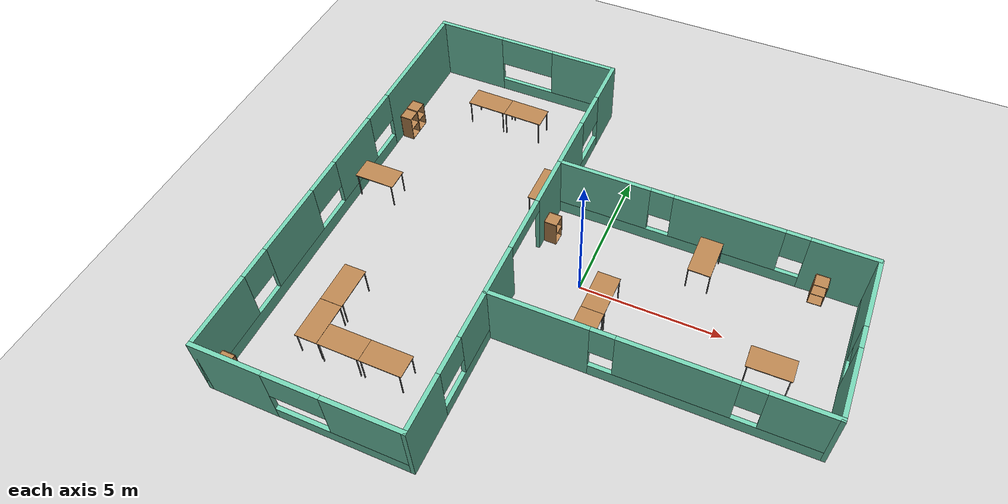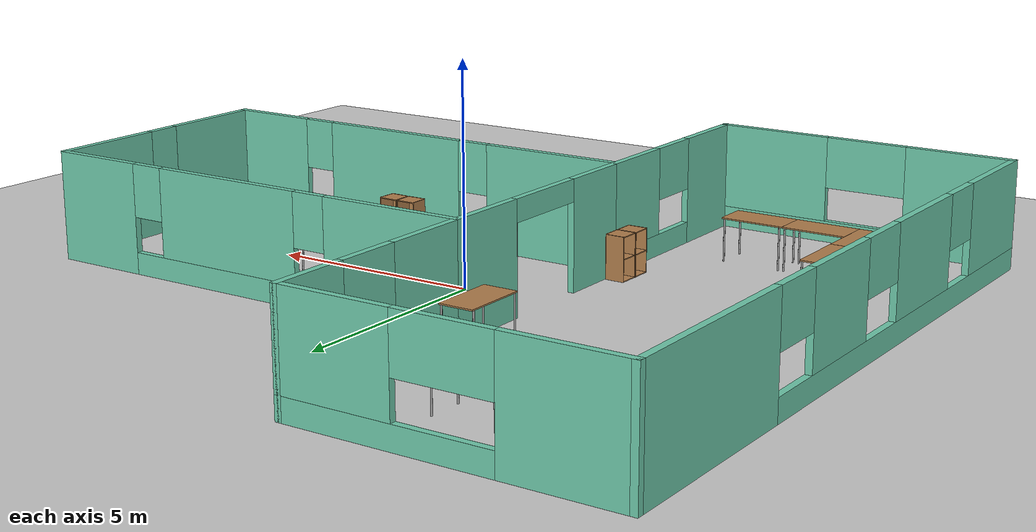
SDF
<sdf version="1.6">
 <world name="default">
  <light name="sun" type="directional">
   <pose>0 0 10 0 -0 0</pose>
   <diffuse>0.8 0.8 0.8 1</diffuse>
   <specular>0.2 0.2 0.2 1</specular>
   <attenuation>
    <range>1000</range>
    <constant>0.9</constant>
    <linear>0.01</linear>
    <quadratic>0.001</quadratic>
   </attenuation>
   <direction>-0.5 0.1 -0.9</direction>
  </light>
  <physics name="default_physics" default="0" type="ode">
   <real_time_update_rate>1000</real_time_update_rate>
   <max_step_size>0.001</max_step_size>
   <real_time_factor>1</real_time_factor>
   <ode>
    <solver>
     <type>quick</type>
     <iters>150</iters>
     <precon_iters>0</precon_iters>
     <sor>1.4</sor>
     <use_dynamic_moi_rescaling>1</use_dynamic_moi_rescaling>
    </solver>
    <constraints>
     <cfm>1e-05</cfm>
     <erp>0.2</erp>
     <contact_max_correcting_vel>2000</contact_max_correcting_vel>
     <contact_surface_layer>0.01</contact_surface_layer>
    </constraints>
   </ode>
  </physics>
  <scene><ambient>0.4 0.4 0.4 1</ambient><background>0.7 0.7 0.7 1</background><shadows>1</shadows></scene>
  <gravity>0 0 -9.8</gravity>
  <magnetic_field>6e-06 2.3e-05 -4.2e-05</magnetic_field>
  <atmosphere type="adiabatic"/>
  <audio><device>default</device></audio>
  <spherical_coordinates>
   <surface_model>EARTH_WGS84</surface_model>
   <latitude_deg>0</latitude_deg>
   <longitude_deg>0</longitude_deg>
   <elevation>0</elevation>
   <heading_deg>0</heading_deg>
  </spherical_coordinates>
  <model name="suelo_new">
   <static>1</static>
   <link name="link">
    <collision name="collision">
     <geometry><plane><normal>0 0 1</normal><size>100 100</size></plane></geometry>
     <surface><friction><ode><mu>100</mu><mu2>50</mu2></ode></friction></surface>
    </collision>
    <visual name="visual">
     <cast_shadows>0</cast_shadows>
     <geometry><plane><normal>0 0 1</normal><size>100 100</size></plane></geometry>
     <material>
      <script>
       <uri>model://suelo_new/materials/scripts</uri>
       <uri>model://suelo_new/materials/textures</uri>
       <name>suelo_new/Diffuse</name>
      </script>
     </material>
    </visual>
   </link>
   <pose>0.210877 -0.017639 0 0 -0 0</pose>
  </model>
  <model name="EnvA">
   <pose>-0.09926 0.078713 0 0 -0 0</pose>
   <link name="Wall_17">
    <pose>-8.99259 0 0 0 -0 -1.5708</pose>
    <visual name="Wall_17_Visual_0">
     <pose>-5.7893 0 1.25 0 -0 0</pose>
     <geometry><box><size>4.67141 0.15 2.5</size></box></geometry>
     <material>
      <script><uri>file://media/materials/scripts/gazebo.material</uri><name>Gazebo/Grey</name></script>
      <ambient>0.435294 0.796078 0.67451 1</ambient>
     </material>
     <meta><layer>0</layer></meta>
    </visual>
    <collision name="Wall_17_Collision_0">
     <geometry><box><size>4.67141 0.15 2.5</size></box></geometry>
     <pose>-5.7893 0 1.25 0 -0 0</pose>
    </collision>
    <visual name="Wall_17_Visual_1">
     <pose>2.3357 0 0.25 0 -0 0</pose>
     <geometry><box><size>11.5786 0.15 0.5</size></box></geometry>
     <material>
      <script><uri>file://media/materials/scripts/gazebo.material</uri><name>Gazebo/Grey</name></script>
      <ambient>0.435294 0.796078 0.67451 1</ambient>
     </material>
     <meta><layer>0</layer></meta>
    </visual>
    <collision name="Wall_17_Collision_1">
     <geometry><box><size>11.5786 0.15 0.5</size></box></geometry>
     <pose>2.3357 0 0.25 0 -0 0</pose>
    </collision>
    <visual name="Wall_17_Visual_2">
     <pose>-0.970133 0 1.5 0 -0 0</pose>
     <geometry><box><size>2.31508 0.15 2</size></box></geometry>
     <material>
      <script><uri>file://media/materials/scripts/gazebo.material</uri><name>Gazebo/Grey</name></script>
      <ambient>0.435294 0.796078 0.67451 1</ambient>
     </material>
     <meta><layer>0</layer></meta>
    </visual>
    <collision name="Wall_17_Collision_2">
     <geometry><box><size>2.31508 0.15 2</size></box></geometry>
     <pose>-0.970133 0 1.5 0 -0 0</pose>
    </collision>
    <visual name="Wall_17_Visual_3">
     <pose>2.93383 0 1.5 0 -0 0</pose>
     <geometry><box><size>2.67918 0.15 2</size></box></geometry>
     <material>
      <script><uri>file://media/materials/scripts/gazebo.material</uri><name>Gazebo/Grey</name></script>
      <ambient>0.435294 0.796078 0.67451 1</ambient>
     </material>
     <meta><layer>0</layer></meta>
    </visual>
    <collision name="Wall_17_Collision_3">
     <geometry><box><size>2.67918 0.15 2</size></box></geometry>
     <pose>2.93383 0 1.5 0 -0 0</pose>
    </collision>
    <visual name="Wall_17_Visual_4">
     <pose>6.78126 0 1.5 0 -0 0</pose>
     <geometry><box><size>2.68748 0.15 2</size></box></geometry>
     <material>
      <script><uri>file://media/materials/scripts/gazebo.material</uri><name>Gazebo/Grey</name></script>
      <ambient>0.435294 0.796078 0.67451 1</ambient>
     </material>
     <meta><layer>0</layer></meta>
    </visual>
    <collision name="Wall_17_Collision_4">
     <geometry><box><size>2.68748 0.15 2</size></box></geometry>
     <pose>6.78126 0 1.5 0 -0 0</pose>
    </collision>
    <visual name="Wall_17_Visual_5">
     <pose>-2.79063 0 1.9 0 -0 0</pose>
     <geometry><box><size>1.32592 0.15 1.2</size></box></geometry>
     <material>
      <script><uri>file://media/materials/scripts/gazebo.material</uri><name>Gazebo/Grey</name></script>
      <ambient>0.435294 0.796078 0.67451 1</ambient>
     </material>
     <meta><layer>0</layer></meta>
    </visual>
    <collision name="Wall_17_Collision_5">
     <geometry><box><size>1.32592 0.15 1.2</size></box></geometry>
     <pose>-2.79063 0 1.9 0 -0 0</pose>
    </collision>
    <visual name="Wall_17_Visual_6">
     <pose>0.890824 0 1.9 0 -0 0</pose>
     <geometry><box><size>1.40683 0.15 1.2</size></box></geometry>
     <material>
      <script><uri>file://media/materials/scripts/gazebo.material</uri><name>Gazebo/Grey</name></script>
      <ambient>0.435294 0.796078 0.67451 1</ambient>
     </material>
     <meta><layer>0</layer></meta>
    </visual>
    <collision name="Wall_17_Collision_6">
     <geometry><box><size>1.40683 0.15 1.2</size></box></geometry>
     <pose>0.890824 0 1.9 0 -0 0</pose>
    </collision>
    <visual name="Wall_17_Visual_7">
     <pose>4.85547 0 1.9 0 -0 0</pose>
     <geometry><box><size>1.1641 0.15 1.2</size></box></geometry>
     <material>
      <script><uri>file://media/materials/scripts/gazebo.material</uri><name>Gazebo/Grey</name></script>
      <ambient>0.435294 0.796078 0.67451 1</ambient>
     </material>
     <meta><layer>0</layer></meta>
    </visual>
    <collision name="Wall_17_Collision_7">
     <geometry><box><size>1.1641 0.15 1.2</size></box></geometry>
     <pose>4.85547 0 1.9 0 -0 0</pose>
    </collision>
   </link>
   <link name="Wall_19">
    <pose>-5.44259 8.05 0 0 -0 0</pose>
    <visual name="Wall_19_Visual_0">
     <pose>-2.31142 0 1.25 0 -0 0</pose>
     <geometry><box><size>2.62715 0.15 2.5</size></box></geometry>
     <material>
      <script><uri>file://media/materials/scripts/gazebo.material</uri><name>Gazebo/Grey</name></script>
      <ambient>0.435294 0.796078 0.67451 1</ambient>
     </material>
     <meta><layer>0</layer></meta>
    </visual>
    <collision name="Wall_19_Collision_0">
     <geometry><box><size>2.62715 0.15 2.5</size></box></geometry>
     <pose>-2.31142 0 1.25 0 -0 0</pose>
    </collision>
    <visual name="Wall_19_Visual_1">
     <pose>1.31358 0 0.25 0 -0 0</pose>
     <geometry><box><size>4.62285 0.15 0.5</size></box></geometry>
     <material>
      <script><uri>file://media/materials/scripts/gazebo.material</uri><name>Gazebo/Grey</name></script>
      <ambient>0.435294 0.796078 0.67451 1</ambient>
     </material>
     <meta><layer>0</layer></meta>
    </visual>
    <collision name="Wall_19_Collision_1">
     <geometry><box><size>4.62285 0.15 0.5</size></box></geometry>
     <pose>1.31358 0 0.25 0 -0 0</pose>
    </collision>
    <visual name="Wall_19_Visual_2">
     <pose>2.36087 0 1.5 0 -0 0</pose>
     <geometry><box><size>2.52827 0.15 2</size></box></geometry>
     <material>
      <script><uri>file://media/materials/scripts/gazebo.material</uri><name>Gazebo/Grey</name></script>
      <ambient>0.435294 0.796078 0.67451 1</ambient>
     </material>
     <meta><layer>0</layer></meta>
    </visual>
    <collision name="Wall_19_Collision_2">
     <geometry><box><size>2.52827 0.15 2</size></box></geometry>
     <pose>2.36087 0 1.5 0 -0 0</pose>
    </collision>
    <visual name="Wall_19_Visual_3">
     <pose>0.049443 0 1.9 0 -0 0</pose>
     <geometry><box><size>2.09458 0.15 1.2</size></box></geometry>
     <material>
      <script><uri>file://media/materials/scripts/gazebo.material</uri><name>Gazebo/Grey</name></script>
      <ambient>0.435294 0.796078 0.67451 1</ambient>
     </material>
     <meta><layer>0</layer></meta>
    </visual>
    <collision name="Wall_19_Collision_3">
     <geometry><box><size>2.09458 0.15 1.2</size></box></geometry>
     <pose>0.049443 0 1.9 0 -0 0</pose>
    </collision>
   </link>
   <link name="Wall_20">
    <pose>-1.89259 5.5 0 0 -0 -1.5708</pose>
    <visual name="Wall_20_Visual_0">
     <pose>-1.7457 0 1.25 0 -0 0</pose>
     <geometry><box><size>1.7586 0.15 2.5</size></box></geometry>
     <material>
      <script><uri>file://media/materials/scripts/gazebo.material</uri><name>Gazebo/Grey</name></script>
      <ambient>0.435294 0.796078 0.67451 1</ambient>
     </material>
     <meta><layer>0</layer></meta>
    </visual>
    <collision name="Wall_20_Collision_0">
     <geometry><box><size>1.7586 0.15 2.5</size></box></geometry>
     <pose>-1.7457 0 1.25 0 -0 0</pose>
    </collision>
    <visual name="Wall_20_Visual_1">
     <pose>0.879302 0 0.25 0 -0 0</pose>
     <geometry><box><size>3.4914 0.15 0.5</size></box></geometry>
     <material>
      <script><uri>file://media/materials/scripts/gazebo.material</uri><name>Gazebo/Grey</name></script>
      <ambient>0.435294 0.796078 0.67451 1</ambient>
     </material>
     <meta><layer>0</layer></meta>
    </visual>
    <collision name="Wall_20_Collision_1">
     <geometry><box><size>3.4914 0.15 0.5</size></box></geometry>
     <pose>0.879302 0 0.25 0 -0 0</pose>
    </collision>
    <visual name="Wall_20_Visual_2">
     <pose>1.60295 0 1.5 0 -0 0</pose>
     <geometry><box><size>2.04411 0.15 2</size></box></geometry>
     <material>
      <script><uri>file://media/materials/scripts/gazebo.material</uri><name>Gazebo/Grey</name></script>
      <ambient>0.435294 0.796078 0.67451 1</ambient>
     </material>
     <meta><layer>0</layer></meta>
    </visual>
    <collision name="Wall_20_Collision_2">
     <geometry><box><size>2.04411 0.15 2</size></box></geometry>
     <pose>1.60295 0 1.5 0 -0 0</pose>
    </collision>
    <visual name="Wall_20_Visual_3">
     <pose>-0.142752 0 1.9 0 -0 0</pose>
     <geometry><box><size>1.44729 0.15 1.2</size></box></geometry>
     <material>
      <script><uri>file://media/materials/scripts/gazebo.material</uri><name>Gazebo/Grey</name></script>
      <ambient>0.435294 0.796078 0.67451 1</ambient>
     </material>
     <meta><layer>0</layer></meta>
    </visual>
    <collision name="Wall_20_Collision_3">
     <geometry><box><size>1.44729 0.15 1.2</size></box></geometry>
     <pose>-0.142752 0 1.9 0 -0 0</pose>
    </collision>
   </link>
   <link name="Wall_27">
    <pose>3.53241 2.9 0 0 -0 3.14159</pose>
    <visual name="Wall_27_Visual_0">
     <pose>-4.37351 0 1.25 0 -0 0</pose>
     <geometry><box><size>2.25298 0.15 2.5</size></box></geometry>
     <material>
      <script><uri>file://media/materials/scripts/gazebo.material</uri><name>Gazebo/Grey</name></script>
      <ambient>0.435294 0.796078 0.67451 1</ambient>
     </material>
     <meta><layer>0</layer></meta>
    </visual>
    <collision name="Wall_27_Collision_0">
     <geometry><box><size>2.25298 0.15 2.5</size></box></geometry>
     <pose>-4.37351 0 1.25 0 -0 0</pose>
    </collision>
    <visual name="Wall_27_Visual_1">
     <pose>1.12649 0 0.25 0 -0 0</pose>
     <geometry><box><size>8.74702 0.15 0.5</size></box></geometry>
     <material>
      <script><uri>file://media/materials/scripts/gazebo.material</uri><name>Gazebo/Grey</name></script>
      <ambient>0.435294 0.796078 0.67451 1</ambient>
     </material>
     <meta><layer>0</layer></meta>
    </visual>
    <collision name="Wall_27_Collision_1">
     <geometry><box><size>8.74702 0.15 0.5</size></box></geometry>
     <pose>1.12649 0 0.25 0 -0 0</pose>
    </collision>
    <visual name="Wall_27_Visual_2">
     <pose>-0.561276 0 1.5 0 -0 0</pose>
     <geometry><box><size>3.77148 0.15 2</size></box></geometry>
     <material>
      <script><uri>file://media/materials/scripts/gazebo.material</uri><name>Gazebo/Grey</name></script>
      <ambient>0.435294 0.796078 0.67451 1</ambient>
     </material>
     <meta><layer>0</layer></meta>
    </visual>
    <collision name="Wall_27_Collision_2">
     <geometry><box><size>3.77148 0.15 2</size></box></geometry>
     <pose>-0.561276 0 1.5 0 -0 0</pose>
    </collision>
    <visual name="Wall_27_Visual_3">
     <pose>3.81223 0 1.5 0 -0 0</pose>
     <geometry><box><size>3.37554 0.15 2</size></box></geometry>
     <material>
      <script><uri>file://media/materials/scripts/gazebo.material</uri><name>Gazebo/Grey</name></script>
      <ambient>0.435294 0.796078 0.67451 1</ambient>
     </material>
     <meta><layer>0</layer></meta>
    </visual>
    <collision name="Wall_27_Collision_3">
     <geometry><box><size>3.37554 0.15 2</size></box></geometry>
     <pose>3.81223 0 1.5 0 -0 0</pose>
    </collision>
    <visual name="Wall_27_Visual_4">
     <pose>-2.84702 0 1.9 0 -0 0</pose>
     <geometry><box><size>0.8 0.15 1.2</size></box></geometry>
     <material>
      <script><uri>file://media/materials/scripts/gazebo.material</uri><name>Gazebo/Grey</name></script>
      <ambient>0.435294 0.796078 0.67451 1</ambient>
     </material>
     <meta><layer>0</layer></meta>
    </visual>
    <collision name="Wall_27_Collision_4">
     <geometry><box><size>0.8 0.15 1.2</size></box></geometry>
     <pose>-2.84702 0 1.9 0 -0 0</pose>
    </collision>
    <visual name="Wall_27_Visual_5">
     <pose>1.72446 0 1.9 0 -0 0</pose>
     <geometry><box><size>0.8 0.15 1.2</size></box></geometry>
     <material>
      <script><uri>file://media/materials/scripts/gazebo.material</uri><name>Gazebo/Grey</name></script>
      <ambient>0.435294 0.796078 0.67451 1</ambient>
     </material>
     <meta><layer>0</layer></meta>
    </visual>
    <collision name="Wall_27_Collision_5">
     <geometry><box><size>0.8 0.15 1.2</size></box></geometry>
     <pose>1.72446 0 1.9 0 -0 0</pose>
    </collision>
   </link>
   <link name="Wall_30">
    <pose>-5.44259 -8.05 0 0 -0 0</pose>
    <visual name="Wall_30_Visual_0">
     <pose>-2.35188 0 1.25 0 -0 0</pose>
     <geometry><box><size>2.54624 0.15 2.5</size></box></geometry>
     <material>
      <script><uri>file://media/materials/scripts/gazebo.material</uri><name>Gazebo/Grey</name></script>
      <ambient>0.435294 0.796078 0.67451 1</ambient>
     </material>
     <meta><layer>0</layer></meta>
    </visual>
    <collision name="Wall_30_Collision_0">
     <geometry><box><size>2.54624 0.15 2.5</size></box></geometry>
     <pose>-2.35188 0 1.25 0 -0 0</pose>
    </collision>
    <visual name="Wall_30_Visual_1">
     <pose>1.27312 0 0.25 0 -0 0</pose>
     <geometry><box><size>4.70376 0.15 0.5</size></box></geometry>
     <material>
      <script><uri>file://media/materials/scripts/gazebo.material</uri><name>Gazebo/Grey</name></script>
      <ambient>0.435294 0.796078 0.67451 1</ambient>
     </material>
     <meta><layer>0</layer></meta>
    </visual>
    <collision name="Wall_30_Collision_1">
     <geometry><box><size>4.70376 0.15 0.5</size></box></geometry>
     <pose>1.27312 0 0.25 0 -0 0</pose>
    </collision>
    <visual name="Wall_30_Visual_2">
     <pose>2.2395 0 1.5 0 -0 0</pose>
     <geometry><box><size>2.771 0.15 2</size></box></geometry>
     <material>
      <script><uri>file://media/materials/scripts/gazebo.material</uri><name>Gazebo/Grey</name></script>
      <ambient>0.435294 0.796078 0.67451 1</ambient>
     </material>
     <meta><layer>0</layer></meta>
    </visual>
    <collision name="Wall_30_Collision_2">
     <geometry><box><size>2.771 0.15 2</size></box></geometry>
     <pose>2.2395 0 1.5 0 -0 0</pose>
    </collision>
    <visual name="Wall_30_Visual_3">
     <pose>-0.11238 0 1.9 0 -0 0</pose>
     <geometry><box><size>1.93276 0.15 1.2</size></box></geometry>
     <material>
      <script><uri>file://media/materials/scripts/gazebo.material</uri><name>Gazebo/Grey</name></script>
      <ambient>0.435294 0.796078 0.67451 1</ambient>
     </material>
     <meta><layer>0</layer></meta>
    </visual>
    <collision name="Wall_30_Collision_3">
     <geometry><box><size>1.93276 0.15 1.2</size></box></geometry>
     <pose>-0.11238 0 1.9 0 -0 0</pose>
    </collision>
   </link>
   <link name="Wall_34">
    <pose>3.56759 -2.98503 0 0 -0 0</pose>
    <visual name="Wall_34_Visual_0">
     <pose>-3.76914 0 1.25 0 -0 0</pose>
     <geometry><box><size>3.46172 0.15 2.5</size></box></geometry>
     <material>
      <script><uri>file://media/materials/scripts/gazebo.material</uri><name>Gazebo/Grey</name></script>
      <ambient>0.435294 0.796078 0.67451 1</ambient>
     </material>
     <meta><layer>0</layer></meta>
    </visual>
    <collision name="Wall_34_Collision_0">
     <geometry><box><size>3.46172 0.15 2.5</size></box></geometry>
     <pose>-3.76914 0 1.25 0 -0 0</pose>
    </collision>
    <visual name="Wall_34_Visual_1">
     <pose>1.73086 0 0.25 0 -0 0</pose>
     <geometry><box><size>7.53828 0.15 0.5</size></box></geometry>
     <material>
      <script><uri>file://media/materials/scripts/gazebo.material</uri><name>Gazebo/Grey</name></script>
      <ambient>0.435294 0.796078 0.67451 1</ambient>
     </material>
     <meta><layer>0</layer></meta>
    </visual>
    <collision name="Wall_34_Collision_1">
     <geometry><box><size>7.53828 0.15 0.5</size></box></geometry>
     <pose>1.73086 0 0.25 0 -0 0</pose>
    </collision>
    <visual name="Wall_34_Visual_2">
     <pose>0.647464 0 1.5 0 -0 0</pose>
     <geometry><box><size>3.77148 0.15 2</size></box></geometry>
     <material>
      <script><uri>file://media/materials/scripts/gazebo.material</uri><name>Gazebo/Grey</name></script>
      <ambient>0.435294 0.796078 0.67451 1</ambient>
     </material>
     <meta><layer>0</layer></meta>
    </visual>
    <collision name="Wall_34_Collision_2">
     <geometry><box><size>3.77148 0.15 2</size></box></geometry>
     <pose>0.647464 0 1.5 0 -0 0</pose>
    </collision>
    <visual name="Wall_34_Visual_3">
     <pose>4.4166 0 1.5 0 -0 0</pose>
     <geometry><box><size>2.1668 0.15 2</size></box></geometry>
     <material>
      <script><uri>file://media/materials/scripts/gazebo.material</uri><name>Gazebo/Grey</name></script>
      <ambient>0.435294 0.796078 0.67451 1</ambient>
     </material>
     <meta><layer>0</layer></meta>
    </visual>
    <collision name="Wall_34_Collision_3">
     <geometry><box><size>2.1668 0.15 2</size></box></geometry>
     <pose>4.4166 0 1.5 0 -0 0</pose>
    </collision>
    <visual name="Wall_34_Visual_4">
     <pose>-1.63828 0 1.9 0 -0 0</pose>
     <geometry><box><size>0.8 0.15 1.2</size></box></geometry>
     <material>
      <script><uri>file://media/materials/scripts/gazebo.material</uri><name>Gazebo/Grey</name></script>
      <ambient>0.435294 0.796078 0.67451 1</ambient>
     </material>
     <meta><layer>0</layer></meta>
    </visual>
    <collision name="Wall_34_Collision_4">
     <geometry><box><size>0.8 0.15 1.2</size></box></geometry>
     <pose>-1.63828 0 1.9 0 -0 0</pose>
    </collision>
    <visual name="Wall_34_Visual_5">
     <pose>2.9332 0 1.9 0 -0 0</pose>
     <geometry><box><size>0.8 0.15 1.2</size></box></geometry>
     <material>
      <script><uri>file://media/materials/scripts/gazebo.material</uri><name>Gazebo/Grey</name></script>
      <ambient>0.435294 0.796078 0.67451 1</ambient>
     </material>
     <meta><layer>0</layer></meta>
    </visual>
    <collision name="Wall_34_Collision_5">
     <geometry><box><size>0.8 0.15 1.2</size></box></geometry>
     <pose>2.9332 0 1.9 0 -0 0</pose>
    </collision>
   </link>
   <link name="Wall_45">
    <pose>-1.89259 -5.5 0 0 -0 1.5708</pose>
    <visual name="Wall_45_Visual_0">
     <pose>-1.60491 0 1.25 0 -0 0</pose>
     <geometry><box><size>2.04019 0.15 2.5</size></box></geometry>
     <material>
      <script><uri>file://media/materials/scripts/gazebo.material</uri><name>Gazebo/Grey</name></script>
      <ambient>0.435294 0.796078 0.67451 1</ambient>
     </material>
     <meta><layer>0</layer></meta>
    </visual>
    <collision name="Wall_45_Collision_0">
     <geometry><box><size>2.04019 0.15 2.5</size></box></geometry>
     <pose>-1.60491 0 1.25 0 -0 0</pose>
    </collision>
    <visual name="Wall_45_Visual_1">
     <pose>1.02009 0 0.25 0 -0 0</pose>
     <geometry><box><size>3.20981 0.15 0.5</size></box></geometry>
     <material>
      <script><uri>file://media/materials/scripts/gazebo.material</uri><name>Gazebo/Grey</name></script>
      <ambient>0.435294 0.796078 0.67451 1</ambient>
     </material>
     <meta><layer>0</layer></meta>
    </visual>
    <collision name="Wall_45_Collision_1">
     <geometry><box><size>3.20981 0.15 0.5</size></box></geometry>
     <pose>1.02009 0 0.25 0 -0 0</pose>
    </collision>
    <visual name="Wall_45_Visual_2">
     <pose>1.68306 0 1.5 0 -0 0</pose>
     <geometry><box><size>1.88389 0.15 2</size></box></geometry>
     <material>
      <script><uri>file://media/materials/scripts/gazebo.material</uri><name>Gazebo/Grey</name></script>
      <ambient>0.435294 0.796078 0.67451 1</ambient>
     </material>
     <meta><layer>0</layer></meta>
    </visual>
    <collision name="Wall_45_Collision_2">
     <geometry><box><size>1.88389 0.15 2</size></box></geometry>
     <pose>1.68306 0 1.5 0 -0 0</pose>
    </collision>
    <visual name="Wall_45_Visual_3">
     <pose>0.078152 0 1.9 0 -0 0</pose>
     <geometry><box><size>1.32592 0.15 1.2</size></box></geometry>
     <material>
      <script><uri>file://media/materials/scripts/gazebo.material</uri><name>Gazebo/Grey</name></script>
      <ambient>0.435294 0.796078 0.67451 1</ambient>
     </material>
     <meta><layer>0</layer></meta>
    </visual>
    <collision name="Wall_45_Collision_3">
     <geometry><box><size>1.32592 0.15 1.2</size></box></geometry>
     <pose>0.078152 0 1.9 0 -0 0</pose>
    </collision>
   </link>
   <link name="Wall_47">
    <pose>8.99259 -0.060028 0 0 -0 1.5708</pose>
    <visual name="Wall_47_Visual_0">
     <pose>-1.72096 0 1.25 0 -0 0</pose>
     <geometry><box><size>2.55809 0.15 2.5</size></box></geometry>
     <material>
      <script><uri>file://media/materials/scripts/gazebo.material</uri><name>Gazebo/Grey</name></script>
      <ambient>0.435294 0.796078 0.67451 1</ambient>
     </material>
     <meta><layer>0</layer></meta>
    </visual>
    <collision name="Wall_47_Collision_0">
     <geometry><box><size>2.55809 0.15 2.5</size></box></geometry>
     <pose>-1.72096 0 1.25 0 -0 0</pose>
    </collision>
    <visual name="Wall_47_Visual_1">
     <pose>1.27904 0 0.25 0 -0 0</pose>
     <geometry><box><size>3.44191 0.15 0.5</size></box></geometry>
     <material>
      <script><uri>file://media/materials/scripts/gazebo.material</uri><name>Gazebo/Grey</name></script>
      <ambient>0.435294 0.796078 0.67451 1</ambient>
     </material>
     <meta><layer>0</layer></meta>
    </visual>
    <collision name="Wall_47_Collision_1">
     <geometry><box><size>3.44191 0.15 0.5</size></box></geometry>
     <pose>1.27904 0 0.25 0 -0 0</pose>
    </collision>
    <visual name="Wall_47_Visual_2">
     <pose>1.67904 0 1.5 0 -0 0</pose>
     <geometry><box><size>2.64191 0.15 2</size></box></geometry>
     <material>
      <script><uri>file://media/materials/scripts/gazebo.material</uri><name>Gazebo/Grey</name></script>
      <ambient>0.435294 0.796078 0.67451 1</ambient>
     </material>
     <meta><layer>0</layer></meta>
    </visual>
    <collision name="Wall_47_Collision_2">
     <geometry><box><size>2.64191 0.15 2</size></box></geometry>
     <pose>1.67904 0 1.5 0 -0 0</pose>
    </collision>
    <visual name="Wall_47_Visual_3">
     <pose>-0.041911 0 1.9 0 -0 0</pose>
     <geometry><box><size>0.8 0.15 1.2</size></box></geometry>
     <material>
      <script><uri>file://media/materials/scripts/gazebo.material</uri><name>Gazebo/Grey</name></script>
      <ambient>0.435294 0.796078 0.67451 1</ambient>
     </material>
     <meta><layer>0</layer></meta>
    </visual>
    <collision name="Wall_47_Collision_3">
     <geometry><box><size>0.8 0.15 1.2</size></box></geometry>
     <pose>-0.041911 0 1.9 0 -0 0</pose>
    </collision>
   </link>
   <link name="Wall_49">
    <pose>-1.89259 -0.025 0 0 -0 1.5708</pose>
    <visual name="Wall_49_Visual_0">
     <pose>-2.06689 0 1.25 0 -0 0</pose>
     <geometry><box><size>1.86623 0.15 2.5</size></box></geometry>
     <material>
      <script><uri>file://media/materials/scripts/gazebo.material</uri><name>Gazebo/Grey</name></script>
      <ambient>0.435294 0.796078 0.67451 1</ambient>
     </material>
     <meta><layer>0</layer></meta>
    </visual>
    <collision name="Wall_49_Collision_0">
     <geometry><box><size>1.86623 0.15 2.5</size></box></geometry>
     <pose>-2.06689 0 1.25 0 -0 0</pose>
    </collision>
    <visual name="Wall_49_Visual_1">
     <pose>1.98995 0 1.25 0 -0 0</pose>
     <geometry><box><size>2.02011 0.15 2.5</size></box></geometry>
     <material>
      <script><uri>file://media/materials/scripts/gazebo.material</uri><name>Gazebo/Grey</name></script>
      <ambient>0.435294 0.796078 0.67451 1</ambient>
     </material>
     <meta><layer>0</layer></meta>
    </visual>
    <collision name="Wall_49_Collision_1">
     <geometry><box><size>2.02011 0.15 2.5</size></box></geometry>
     <pose>1.98995 0 1.25 0 -0 0</pose>
    </collision>
    <visual name="Wall_49_Visual_2">
     <pose>-0.07694 0 2.25 0 -0 0</pose>
     <geometry><box><size>2.11367 0.15 0.5</size></box></geometry>
     <material>
      <script><uri>file://media/materials/scripts/gazebo.material</uri><name>Gazebo/Grey</name></script>
      <ambient>0.435294 0.796078 0.67451 1</ambient>
     </material>
     <meta><layer>0</layer></meta>
    </visual>
    <collision name="Wall_49_Collision_2">
     <geometry><box><size>2.11367 0.15 0.5</size></box></geometry>
     <pose>-0.07694 0 2.25 0 -0 0</pose>
    </collision>
   </link>
   <static>1</static>
  </model>
  <model name="table">
   <static>1</static>
   <link name="link">
    <collision name="surface">
     <pose>0 0 1 0 -0 0</pose>
     <geometry><box><size>1.5 0.8 0.03</size></box></geometry>
     <surface><friction><ode><mu>0.6</mu><mu2>0.6</mu2></ode></friction></surface>
    </collision>
    <visual name="visual1">
     <pose>0 0 1 0 -0 0</pose>
     <geometry><box><size>1.5 0.8 0.03</size></box></geometry>
     <material>
      <script><uri>file://media/materials/scripts/gazebo.material</uri><name>Gazebo/Wood</name></script>
     </material>
    </visual>
    <collision name="front_left_leg">
     <pose>0.68 0.38 0.5 0 -0 0</pose>
     <geometry><cylinder><radius>0.02</radius><length>1</length></cylinder></geometry>
    </collision>
    <visual name="front_left_leg">
     <pose>0.68 0.38 0.5 0 -0 0</pose>
     <geometry><cylinder><radius>0.02</radius><length>1</length></cylinder></geometry>
     <material>
      <script><uri>file://media/materials/scripts/gazebo.material</uri><name>Gazebo/Grey</name></script>
     </material>
    </visual>
    <collision name="front_right_leg">
     <pose>0.68 -0.38 0.5 0 -0 0</pose>
     <geometry><cylinder><radius>0.02</radius><length>1</length></cylinder></geometry>
    </collision>
    <visual name="front_right_leg">
     <pose>0.68 -0.38 0.5 0 -0 0</pose>
     <geometry><cylinder><radius>0.02</radius><length>1</length></cylinder></geometry>
     <material>
      <script><uri>file://media/materials/scripts/gazebo.material</uri><name>Gazebo/Grey</name></script>
     </material>
    </visual>
    <collision name="back_right_leg">
     <pose>-0.68 -0.38 0.5 0 -0 0</pose>
     <geometry><cylinder><radius>0.02</radius><length>1</length></cylinder></geometry>
    </collision>
    <visual name="back_right_leg">
     <pose>-0.68 -0.38 0.5 0 -0 0</pose>
     <geometry><cylinder><radius>0.02</radius><length>1</length></cylinder></geometry>
     <material>
      <script><uri>file://media/materials/scripts/gazebo.material</uri><name>Gazebo/Grey</name></script>
     </material>
    </visual>
    <collision name="back_left_leg">
     <pose>-0.68 0.38 0.5 0 -0 0</pose>
     <geometry><cylinder><radius>0.02</radius><length>1</length></cylinder></geometry>
    </collision>
    <visual name="back_left_leg">
     <pose>-0.68 0.38 0.5 0 -0 0</pose>
     <geometry><cylinder><radius>0.02</radius><length>1</length></cylinder></geometry>
     <material>
      <script><uri>file://media/materials/scripts/gazebo.material</uri><name>Gazebo/Grey</name></script>
     </material>
    </visual>
   </link>
   <pose>0.935446 -2.0806 0 0 -0 1.56084</pose>
  </model>
  <model name="table_clone">
   <static>1</static>
   <link name="link">
    <collision name="surface">
     <pose>0 0 1 0 -0 0</pose>
     <geometry><box><size>1.5 0.8 0.03</size></box></geometry>
     <surface><friction><ode><mu>0.6</mu><mu2>0.6</mu2></ode></friction></surface>
    </collision>
    <visual name="visual1">
     <pose>0 0 1 0 -0 0</pose>
     <geometry><box><size>1.5 0.8 0.03</size></box></geometry>
     <material>
      <script><uri>file://media/materials/scripts/gazebo.material</uri><name>Gazebo/Wood</name></script>
     </material>
    </visual>
    <collision name="front_left_leg">
     <pose>0.68 0.38 0.5 0 -0 0</pose>
     <geometry><cylinder><radius>0.02</radius><length>1</length></cylinder></geometry>
    </collision>
    <visual name="front_left_leg">
     <pose>0.68 0.38 0.5 0 -0 0</pose>
     <geometry><cylinder><radius>0.02</radius><length>1</length></cylinder></geometry>
     <material>
      <script><uri>file://media/materials/scripts/gazebo.material</uri><name>Gazebo/Grey</name></script>
     </material>
    </visual>
    <collision name="front_right_leg">
     <pose>0.68 -0.38 0.5 0 -0 0</pose>
     <geometry><cylinder><radius>0.02</radius><length>1</length></cylinder></geometry>
    </collision>
    <visual name="front_right_leg">
     <pose>0.68 -0.38 0.5 0 -0 0</pose>
     <geometry><cylinder><radius>0.02</radius><length>1</length></cylinder></geometry>
     <material>
      <script><uri>file://media/materials/scripts/gazebo.material</uri><name>Gazebo/Grey</name></script>
     </material>
    </visual>
    <collision name="back_right_leg">
     <pose>-0.68 -0.38 0.5 0 -0 0</pose>
     <geometry><cylinder><radius>0.02</radius><length>1</length></cylinder></geometry>
    </collision>
    <visual name="back_right_leg">
     <pose>-0.68 -0.38 0.5 0 -0 0</pose>
     <geometry><cylinder><radius>0.02</radius><length>1</length></cylinder></geometry>
     <material>
      <script><uri>file://media/materials/scripts/gazebo.material</uri><name>Gazebo/Grey</name></script>
     </material>
    </visual>
    <collision name="back_left_leg">
     <pose>-0.68 0.38 0.5 0 -0 0</pose>
     <geometry><cylinder><radius>0.02</radius><length>1</length></cylinder></geometry>
    </collision>
    <visual name="back_left_leg">
     <pose>-0.68 0.38 0.5 0 -0 0</pose>
     <geometry><cylinder><radius>0.02</radius><length>1</length></cylinder></geometry>
     <material>
      <script><uri>file://media/materials/scripts/gazebo.material</uri><name>Gazebo/Grey</name></script>
     </material>
    </visual>
   </link>
   <pose>0.954915 -0.582595 0 0 -0 1.56084</pose>
  </model>
  <model name="table_clone_clone">
   <static>1</static>
   <link name="link">
    <collision name="surface">
     <pose>0 0 1 0 -0 0</pose>
     <geometry><box><size>1.5 0.8 0.03</size></box></geometry>
     <surface><friction><ode><mu>0.6</mu><mu2>0.6</mu2></ode></friction></surface>
    </collision>
    <visual name="visual1">
     <pose>0 0 1 0 -0 0</pose>
     <geometry><box><size>1.5 0.8 0.03</size></box></geometry>
     <material>
      <script><uri>file://media/materials/scripts/gazebo.material</uri><name>Gazebo/Wood</name></script>
     </material>
    </visual>
    <collision name="front_left_leg">
     <pose>0.68 0.38 0.5 0 -0 0</pose>
     <geometry><cylinder><radius>0.02</radius><length>1</length></cylinder></geometry>
    </collision>
    <visual name="front_left_leg">
     <pose>0.68 0.38 0.5 0 -0 0</pose>
     <geometry><cylinder><radius>0.02</radius><length>1</length></cylinder></geometry>
     <material>
      <script><uri>file://media/materials/scripts/gazebo.material</uri><name>Gazebo/Grey</name></script>
     </material>
    </visual>
    <collision name="front_right_leg">
     <pose>0.68 -0.38 0.5 0 -0 0</pose>
     <geometry><cylinder><radius>0.02</radius><length>1</length></cylinder></geometry>
    </collision>
    <visual name="front_right_leg">
     <pose>0.68 -0.38 0.5 0 -0 0</pose>
     <geometry><cylinder><radius>0.02</radius><length>1</length></cylinder></geometry>
     <material>
      <script><uri>file://media/materials/scripts/gazebo.material</uri><name>Gazebo/Grey</name></script>
     </material>
    </visual>
    <collision name="back_right_leg">
     <pose>-0.68 -0.38 0.5 0 -0 0</pose>
     <geometry><cylinder><radius>0.02</radius><length>1</length></cylinder></geometry>
    </collision>
    <visual name="back_right_leg">
     <pose>-0.68 -0.38 0.5 0 -0 0</pose>
     <geometry><cylinder><radius>0.02</radius><length>1</length></cylinder></geometry>
     <material>
      <script><uri>file://media/materials/scripts/gazebo.material</uri><name>Gazebo/Grey</name></script>
     </material>
    </visual>
    <collision name="back_left_leg">
     <pose>-0.68 0.38 0.5 0 -0 0</pose>
     <geometry><cylinder><radius>0.02</radius><length>1</length></cylinder></geometry>
    </collision>
    <visual name="back_left_leg">
     <pose>-0.68 0.38 0.5 0 -0 0</pose>
     <geometry><cylinder><radius>0.02</radius><length>1</length></cylinder></geometry>
     <material>
      <script><uri>file://media/materials/scripts/gazebo.material</uri><name>Gazebo/Grey</name></script>
     </material>
    </visual>
   </link>
   <pose>3.64772 2.15257 0 0 -0 1.56084</pose>
  </model>
  <model name="table_clone_clone_0_clone">
   <static>1</static>
   <link name="link">
    <collision name="surface">
     <pose>0 0 1 0 -0 0</pose>
     <geometry><box><size>1.5 0.8 0.03</size></box></geometry>
     <surface><friction><ode><mu>0.6</mu><mu2>0.6</mu2></ode></friction></surface>
    </collision>
    <visual name="visual1">
     <pose>0 0 1 0 -0 0</pose>
     <geometry><box><size>1.5 0.8 0.03</size></box></geometry>
     <material>
      <script><uri>file://media/materials/scripts/gazebo.material</uri><name>Gazebo/Wood</name></script>
     </material>
    </visual>
    <collision name="front_left_leg">
     <pose>0.68 0.38 0.5 0 -0 0</pose>
     <geometry><cylinder><radius>0.02</radius><length>1</length></cylinder></geometry>
    </collision>
    <visual name="front_left_leg">
     <pose>0.68 0.38 0.5 0 -0 0</pose>
     <geometry><cylinder><radius>0.02</radius><length>1</length></cylinder></geometry>
     <material>
      <script><uri>file://media/materials/scripts/gazebo.material</uri><name>Gazebo/Grey</name></script>
     </material>
    </visual>
    <collision name="front_right_leg">
     <pose>0.68 -0.38 0.5 0 -0 0</pose>
     <geometry><cylinder><radius>0.02</radius><length>1</length></cylinder></geometry>
    </collision>
    <visual name="front_right_leg">
     <pose>0.68 -0.38 0.5 0 -0 0</pose>
     <geometry><cylinder><radius>0.02</radius><length>1</length></cylinder></geometry>
     <material>
      <script><uri>file://media/materials/scripts/gazebo.material</uri><name>Gazebo/Grey</name></script>
     </material>
    </visual>
    <collision name="back_right_leg">
     <pose>-0.68 -0.38 0.5 0 -0 0</pose>
     <geometry><cylinder><radius>0.02</radius><length>1</length></cylinder></geometry>
    </collision>
    <visual name="back_right_leg">
     <pose>-0.68 -0.38 0.5 0 -0 0</pose>
     <geometry><cylinder><radius>0.02</radius><length>1</length></cylinder></geometry>
     <material>
      <script><uri>file://media/materials/scripts/gazebo.material</uri><name>Gazebo/Grey</name></script>
     </material>
    </visual>
    <collision name="back_left_leg">
     <pose>-0.68 0.38 0.5 0 -0 0</pose>
     <geometry><cylinder><radius>0.02</radius><length>1</length></cylinder></geometry>
    </collision>
    <visual name="back_left_leg">
     <pose>-0.68 0.38 0.5 0 -0 0</pose>
     <geometry><cylinder><radius>0.02</radius><length>1</length></cylinder></geometry>
     <material>
      <script><uri>file://media/materials/scripts/gazebo.material</uri><name>Gazebo/Grey</name></script>
     </material>
    </visual>
   </link>
   <pose>6.69355 -0.905261 -0.133705 0 0 -3.13123</pose>
  </model>
  <model name="table_clone_clone_1">
   <static>1</static>
   <link name="link">
    <collision name="surface">
     <pose>0 0 1 0 -0 0</pose>
     <geometry><box><size>1.5 0.8 0.03</size></box></geometry>
     <surface><friction><ode><mu>0.6</mu><mu2>0.6</mu2></ode></friction></surface>
    </collision>
    <visual name="visual1">
     <pose>0 0 1 0 -0 0</pose>
     <geometry><box><size>1.5 0.8 0.03</size></box></geometry>
     <material>
      <script><uri>file://media/materials/scripts/gazebo.material</uri><name>Gazebo/Wood</name></script>
     </material>
    </visual>
    <collision name="front_left_leg">
     <pose>0.68 0.38 0.5 0 -0 0</pose>
     <geometry><cylinder><radius>0.02</radius><length>1</length></cylinder></geometry>
    </collision>
    <visual name="front_left_leg">
     <pose>0.68 0.38 0.5 0 -0 0</pose>
     <geometry><cylinder><radius>0.02</radius><length>1</length></cylinder></geometry>
     <material>
      <script><uri>file://media/materials/scripts/gazebo.material</uri><name>Gazebo/Grey</name></script>
     </material>
    </visual>
    <collision name="front_right_leg">
     <pose>0.68 -0.38 0.5 0 -0 0</pose>
     <geometry><cylinder><radius>0.02</radius><length>1</length></cylinder></geometry>
    </collision>
    <visual name="front_right_leg">
     <pose>0.68 -0.38 0.5 0 -0 0</pose>
     <geometry><cylinder><radius>0.02</radius><length>1</length></cylinder></geometry>
     <material>
      <script><uri>file://media/materials/scripts/gazebo.material</uri><name>Gazebo/Grey</name></script>
     </material>
    </visual>
    <collision name="back_right_leg">
     <pose>-0.68 -0.38 0.5 0 -0 0</pose>
     <geometry><cylinder><radius>0.02</radius><length>1</length></cylinder></geometry>
    </collision>
    <visual name="back_right_leg">
     <pose>-0.68 -0.38 0.5 0 -0 0</pose>
     <geometry><cylinder><radius>0.02</radius><length>1</length></cylinder></geometry>
     <material>
      <script><uri>file://media/materials/scripts/gazebo.material</uri><name>Gazebo/Grey</name></script>
     </material>
    </visual>
    <collision name="back_left_leg">
     <pose>-0.68 0.38 0.5 0 -0 0</pose>
     <geometry><cylinder><radius>0.02</radius><length>1</length></cylinder></geometry>
    </collision>
    <visual name="back_left_leg">
     <pose>-0.68 0.38 0.5 0 -0 0</pose>
     <geometry><cylinder><radius>0.02</radius><length>1</length></cylinder></geometry>
     <material>
      <script><uri>file://media/materials/scripts/gazebo.material</uri><name>Gazebo/Grey</name></script>
     </material>
    </visual>
   </link>
   <pose>-6.87483 -5.09975 0 0 -0 1.56881</pose>
  </model>
  <model name="table_clone_clone_2">
   <static>1</static>
   <link name="link">
    <collision name="surface">
     <pose>0 0 1 0 -0 0</pose>
     <geometry><box><size>1.5 0.8 0.03</size></box></geometry>
     <surface><friction><ode><mu>0.6</mu><mu2>0.6</mu2></ode></friction></surface>
    </collision>
    <visual name="visual1">
     <pose>0 0 1 0 -0 0</pose>
     <geometry><box><size>1.5 0.8 0.03</size></box></geometry>
     <material>
      <script><uri>file://media/materials/scripts/gazebo.material</uri><name>Gazebo/Wood</name></script>
     </material>
    </visual>
    <collision name="front_left_leg">
     <pose>0.68 0.38 0.5 0 -0 0</pose>
     <geometry><cylinder><radius>0.02</radius><length>1</length></cylinder></geometry>
    </collision>
    <visual name="front_left_leg">
     <pose>0.68 0.38 0.5 0 -0 0</pose>
     <geometry><cylinder><radius>0.02</radius><length>1</length></cylinder></geometry>
     <material>
      <script><uri>file://media/materials/scripts/gazebo.material</uri><name>Gazebo/Grey</name></script>
     </material>
    </visual>
    <collision name="front_right_leg">
     <pose>0.68 -0.38 0.5 0 -0 0</pose>
     <geometry><cylinder><radius>0.02</radius><length>1</length></cylinder></geometry>
    </collision>
    <visual name="front_right_leg">
     <pose>0.68 -0.38 0.5 0 -0 0</pose>
     <geometry><cylinder><radius>0.02</radius><length>1</length></cylinder></geometry>
     <material>
      <script><uri>file://media/materials/scripts/gazebo.material</uri><name>Gazebo/Grey</name></script>
     </material>
    </visual>
    <collision name="back_right_leg">
     <pose>-0.68 -0.38 0.5 0 -0 0</pose>
     <geometry><cylinder><radius>0.02</radius><length>1</length></cylinder></geometry>
    </collision>
    <visual name="back_right_leg">
     <pose>-0.68 -0.38 0.5 0 -0 0</pose>
     <geometry><cylinder><radius>0.02</radius><length>1</length></cylinder></geometry>
     <material>
      <script><uri>file://media/materials/scripts/gazebo.material</uri><name>Gazebo/Grey</name></script>
     </material>
    </visual>
    <collision name="back_left_leg">
     <pose>-0.68 0.38 0.5 0 -0 0</pose>
     <geometry><cylinder><radius>0.02</radius><length>1</length></cylinder></geometry>
    </collision>
    <visual name="back_left_leg">
     <pose>-0.68 0.38 0.5 0 -0 0</pose>
     <geometry><cylinder><radius>0.02</radius><length>1</length></cylinder></geometry>
     <material>
      <script><uri>file://media/materials/scripts/gazebo.material</uri><name>Gazebo/Grey</name></script>
     </material>
    </visual>
   </link>
   <pose>-6.86927 -3.59813 0 0 -0 1.56849</pose>
  </model>
  <model name="table_clone_clone_3">
   <static>1</static>
   <link name="link">
    <collision name="surface">
     <pose>0 0 1 0 -0 0</pose>
     <geometry><box><size>1.5 0.8 0.03</size></box></geometry>
     <surface><friction><ode><mu>0.6</mu><mu2>0.6</mu2></ode></friction></surface>
    </collision>
    <visual name="visual1">
     <pose>0 0 1 0 -0 0</pose>
     <geometry><box><size>1.5 0.8 0.03</size></box></geometry>
     <material>
      <script><uri>file://media/materials/scripts/gazebo.material</uri><name>Gazebo/Wood</name></script>
     </material>
    </visual>
    <collision name="front_left_leg">
     <pose>0.68 0.38 0.5 0 -0 0</pose>
     <geometry><cylinder><radius>0.02</radius><length>1</length></cylinder></geometry>
    </collision>
    <visual name="front_left_leg">
     <pose>0.68 0.38 0.5 0 -0 0</pose>
     <geometry><cylinder><radius>0.02</radius><length>1</length></cylinder></geometry>
     <material>
      <script><uri>file://media/materials/scripts/gazebo.material</uri><name>Gazebo/Grey</name></script>
     </material>
    </visual>
    <collision name="front_right_leg">
     <pose>0.68 -0.38 0.5 0 -0 0</pose>
     <geometry><cylinder><radius>0.02</radius><length>1</length></cylinder></geometry>
    </collision>
    <visual name="front_right_leg">
     <pose>0.68 -0.38 0.5 0 -0 0</pose>
     <geometry><cylinder><radius>0.02</radius><length>1</length></cylinder></geometry>
     <material>
      <script><uri>file://media/materials/scripts/gazebo.material</uri><name>Gazebo/Grey</name></script>
     </material>
    </visual>
    <collision name="back_right_leg">
     <pose>-0.68 -0.38 0.5 0 -0 0</pose>
     <geometry><cylinder><radius>0.02</radius><length>1</length></cylinder></geometry>
    </collision>
    <visual name="back_right_leg">
     <pose>-0.68 -0.38 0.5 0 -0 0</pose>
     <geometry><cylinder><radius>0.02</radius><length>1</length></cylinder></geometry>
     <material>
      <script><uri>file://media/materials/scripts/gazebo.material</uri><name>Gazebo/Grey</name></script>
     </material>
    </visual>
    <collision name="back_left_leg">
     <pose>-0.68 0.38 0.5 0 -0 0</pose>
     <geometry><cylinder><radius>0.02</radius><length>1</length></cylinder></geometry>
    </collision>
    <visual name="back_left_leg">
     <pose>-0.68 0.38 0.5 0 -0 0</pose>
     <geometry><cylinder><radius>0.02</radius><length>1</length></cylinder></geometry>
     <material>
      <script><uri>file://media/materials/scripts/gazebo.material</uri><name>Gazebo/Grey</name></script>
     </material>
    </visual>
   </link>
   <pose>-5.72264 -5.45337 0 0 0 -0.004485</pose>
  </model>
  <model name="table_clone_clone_4">
   <static>1</static>
   <link name="link">
    <collision name="surface">
     <pose>0 0 1 0 -0 0</pose>
     <geometry><box><size>1.5 0.8 0.03</size></box></geometry>
     <surface><friction><ode><mu>0.6</mu><mu2>0.6</mu2></ode></friction></surface>
    </collision>
    <visual name="visual1">
     <pose>0 0 1 0 -0 0</pose>
     <geometry><box><size>1.5 0.8 0.03</size></box></geometry>
     <material>
      <script><uri>file://media/materials/scripts/gazebo.material</uri><name>Gazebo/Wood</name></script>
     </material>
    </visual>
    <collision name="front_left_leg">
     <pose>0.68 0.38 0.5 0 -0 0</pose>
     <geometry><cylinder><radius>0.02</radius><length>1</length></cylinder></geometry>
    </collision>
    <visual name="front_left_leg">
     <pose>0.68 0.38 0.5 0 -0 0</pose>
     <geometry><cylinder><radius>0.02</radius><length>1</length></cylinder></geometry>
     <material>
      <script><uri>file://media/materials/scripts/gazebo.material</uri><name>Gazebo/Grey</name></script>
     </material>
    </visual>
    <collision name="front_right_leg">
     <pose>0.68 -0.38 0.5 0 -0 0</pose>
     <geometry><cylinder><radius>0.02</radius><length>1</length></cylinder></geometry>
    </collision>
    <visual name="front_right_leg">
     <pose>0.68 -0.38 0.5 0 -0 0</pose>
     <geometry><cylinder><radius>0.02</radius><length>1</length></cylinder></geometry>
     <material>
      <script><uri>file://media/materials/scripts/gazebo.material</uri><name>Gazebo/Grey</name></script>
     </material>
    </visual>
    <collision name="back_right_leg">
     <pose>-0.68 -0.38 0.5 0 -0 0</pose>
     <geometry><cylinder><radius>0.02</radius><length>1</length></cylinder></geometry>
    </collision>
    <visual name="back_right_leg">
     <pose>-0.68 -0.38 0.5 0 -0 0</pose>
     <geometry><cylinder><radius>0.02</radius><length>1</length></cylinder></geometry>
     <material>
      <script><uri>file://media/materials/scripts/gazebo.material</uri><name>Gazebo/Grey</name></script>
     </material>
    </visual>
    <collision name="back_left_leg">
     <pose>-0.68 0.38 0.5 0 -0 0</pose>
     <geometry><cylinder><radius>0.02</radius><length>1</length></cylinder></geometry>
    </collision>
    <visual name="back_left_leg">
     <pose>-0.68 0.38 0.5 0 -0 0</pose>
     <geometry><cylinder><radius>0.02</radius><length>1</length></cylinder></geometry>
     <material>
      <script><uri>file://media/materials/scripts/gazebo.material</uri><name>Gazebo/Grey</name></script>
     </material>
    </visual>
   </link>
   <pose>-4.22221 -5.45993 0 0 0 -0.00315</pose>
  </model>
  <model name="table_clone_clone_2_clone">
   <static>1</static>
   <link name="link">
    <collision name="surface">
     <pose>0 0 1 0 -0 0</pose>
     <geometry><box><size>1.5 0.8 0.03</size></box></geometry>
     <surface><friction><ode><mu>0.6</mu><mu2>0.6</mu2></ode></friction></surface>
    </collision>
    <visual name="visual1">
     <pose>0 0 1 0 -0 0</pose>
     <geometry><box><size>1.5 0.8 0.03</size></box></geometry>
     <material>
      <script><uri>file://media/materials/scripts/gazebo.material</uri><name>Gazebo/Wood</name></script>
     </material>
    </visual>
    <collision name="front_left_leg">
     <pose>0.68 0.38 0.5 0 -0 0</pose>
     <geometry><cylinder><radius>0.02</radius><length>1</length></cylinder></geometry>
    </collision>
    <visual name="front_left_leg">
     <pose>0.68 0.38 0.5 0 -0 0</pose>
     <geometry><cylinder><radius>0.02</radius><length>1</length></cylinder></geometry>
     <material>
      <script><uri>file://media/materials/scripts/gazebo.material</uri><name>Gazebo/Grey</name></script>
     </material>
    </visual>
    <collision name="front_right_leg">
     <pose>0.68 -0.38 0.5 0 -0 0</pose>
     <geometry><cylinder><radius>0.02</radius><length>1</length></cylinder></geometry>
    </collision>
    <visual name="front_right_leg">
     <pose>0.68 -0.38 0.5 0 -0 0</pose>
     <geometry><cylinder><radius>0.02</radius><length>1</length></cylinder></geometry>
     <material>
      <script><uri>file://media/materials/scripts/gazebo.material</uri><name>Gazebo/Grey</name></script>
     </material>
    </visual>
    <collision name="back_right_leg">
     <pose>-0.68 -0.38 0.5 0 -0 0</pose>
     <geometry><cylinder><radius>0.02</radius><length>1</length></cylinder></geometry>
    </collision>
    <visual name="back_right_leg">
     <pose>-0.68 -0.38 0.5 0 -0 0</pose>
     <geometry><cylinder><radius>0.02</radius><length>1</length></cylinder></geometry>
     <material>
      <script><uri>file://media/materials/scripts/gazebo.material</uri><name>Gazebo/Grey</name></script>
     </material>
    </visual>
    <collision name="back_left_leg">
     <pose>-0.68 0.38 0.5 0 -0 0</pose>
     <geometry><cylinder><radius>0.02</radius><length>1</length></cylinder></geometry>
    </collision>
    <visual name="back_left_leg">
     <pose>-0.68 0.38 0.5 0 -0 0</pose>
     <geometry><cylinder><radius>0.02</radius><length>1</length></cylinder></geometry>
     <material>
      <script><uri>file://media/materials/scripts/gazebo.material</uri><name>Gazebo/Grey</name></script>
     </material>
    </visual>
   </link>
   <pose>-8.25767 1.13785 0 0 0 -0.000702</pose>
  </model>
  <model name="table_clone_clone_2_clone_clone">
   <static>1</static>
   <link name="link">
    <collision name="surface">
     <pose>0 0 1 0 -0 0</pose>
     <geometry><box><size>1.5 0.8 0.03</size></box></geometry>
     <surface><friction><ode><mu>0.6</mu><mu2>0.6</mu2></ode></friction></surface>
    </collision>
    <visual name="visual1">
     <pose>0 0 1 0 -0 0</pose>
     <geometry><box><size>1.5 0.8 0.03</size></box></geometry>
     <material>
      <script><uri>file://media/materials/scripts/gazebo.material</uri><name>Gazebo/Wood</name></script>
     </material>
    </visual>
    <collision name="front_left_leg">
     <pose>0.68 0.38 0.5 0 -0 0</pose>
     <geometry><cylinder><radius>0.02</radius><length>1</length></cylinder></geometry>
    </collision>
    <visual name="front_left_leg">
     <pose>0.68 0.38 0.5 0 -0 0</pose>
     <geometry><cylinder><radius>0.02</radius><length>1</length></cylinder></geometry>
     <material>
      <script><uri>file://media/materials/scripts/gazebo.material</uri><name>Gazebo/Grey</name></script>
     </material>
    </visual>
    <collision name="front_right_leg">
     <pose>0.68 -0.38 0.5 0 -0 0</pose>
     <geometry><cylinder><radius>0.02</radius><length>1</length></cylinder></geometry>
    </collision>
    <visual name="front_right_leg">
     <pose>0.68 -0.38 0.5 0 -0 0</pose>
     <geometry><cylinder><radius>0.02</radius><length>1</length></cylinder></geometry>
     <material>
      <script><uri>file://media/materials/scripts/gazebo.material</uri><name>Gazebo/Grey</name></script>
     </material>
    </visual>
    <collision name="back_right_leg">
     <pose>-0.68 -0.38 0.5 0 -0 0</pose>
     <geometry><cylinder><radius>0.02</radius><length>1</length></cylinder></geometry>
    </collision>
    <visual name="back_right_leg">
     <pose>-0.68 -0.38 0.5 0 -0 0</pose>
     <geometry><cylinder><radius>0.02</radius><length>1</length></cylinder></geometry>
     <material>
      <script><uri>file://media/materials/scripts/gazebo.material</uri><name>Gazebo/Grey</name></script>
     </material>
    </visual>
    <collision name="back_left_leg">
     <pose>-0.68 0.38 0.5 0 -0 0</pose>
     <geometry><cylinder><radius>0.02</radius><length>1</length></cylinder></geometry>
    </collision>
    <visual name="back_left_leg">
     <pose>-0.68 0.38 0.5 0 -0 0</pose>
     <geometry><cylinder><radius>0.02</radius><length>1</length></cylinder></geometry>
     <material>
      <script><uri>file://media/materials/scripts/gazebo.material</uri><name>Gazebo/Grey</name></script>
     </material>
    </visual>
   </link>
   <pose>-6.17841 6.14008 0 0 0 -0.016556</pose>
  </model>
  <model name="table_clone_clone_2_clone_clone_0">
   <static>1</static>
   <link name="link">
    <collision name="surface">
     <pose>0 0 1 0 -0 0</pose>
     <geometry><box><size>1.5 0.8 0.03</size></box></geometry>
     <surface><friction><ode><mu>0.6</mu><mu2>0.6</mu2></ode></friction></surface>
    </collision>
    <visual name="visual1">
     <pose>0 0 1 0 -0 0</pose>
     <geometry><box><size>1.5 0.8 0.03</size></box></geometry>
     <material>
      <script><uri>file://media/materials/scripts/gazebo.material</uri><name>Gazebo/Wood</name></script>
     </material>
    </visual>
    <collision name="front_left_leg">
     <pose>0.68 0.38 0.5 0 -0 0</pose>
     <geometry><cylinder><radius>0.02</radius><length>1</length></cylinder></geometry>
    </collision>
    <visual name="front_left_leg">
     <pose>0.68 0.38 0.5 0 -0 0</pose>
     <geometry><cylinder><radius>0.02</radius><length>1</length></cylinder></geometry>
     <material>
      <script><uri>file://media/materials/scripts/gazebo.material</uri><name>Gazebo/Grey</name></script>
     </material>
    </visual>
    <collision name="front_right_leg">
     <pose>0.68 -0.38 0.5 0 -0 0</pose>
     <geometry><cylinder><radius>0.02</radius><length>1</length></cylinder></geometry>
    </collision>
    <visual name="front_right_leg">
     <pose>0.68 -0.38 0.5 0 -0 0</pose>
     <geometry><cylinder><radius>0.02</radius><length>1</length></cylinder></geometry>
     <material>
      <script><uri>file://media/materials/scripts/gazebo.material</uri><name>Gazebo/Grey</name></script>
     </material>
    </visual>
    <collision name="back_right_leg">
     <pose>-0.68 -0.38 0.5 0 -0 0</pose>
     <geometry><cylinder><radius>0.02</radius><length>1</length></cylinder></geometry>
    </collision>
    <visual name="back_right_leg">
     <pose>-0.68 -0.38 0.5 0 -0 0</pose>
     <geometry><cylinder><radius>0.02</radius><length>1</length></cylinder></geometry>
     <material>
      <script><uri>file://media/materials/scripts/gazebo.material</uri><name>Gazebo/Grey</name></script>
     </material>
    </visual>
    <collision name="back_left_leg">
     <pose>-0.68 0.38 0.5 0 -0 0</pose>
     <geometry><cylinder><radius>0.02</radius><length>1</length></cylinder></geometry>
    </collision>
    <visual name="back_left_leg">
     <pose>-0.68 0.38 0.5 0 -0 0</pose>
     <geometry><cylinder><radius>0.02</radius><length>1</length></cylinder></geometry>
     <material>
      <script><uri>file://media/materials/scripts/gazebo.material</uri><name>Gazebo/Grey</name></script>
     </material>
    </visual>
   </link>
   <pose>-4.67945 6.11581 0 0 0 -0.016556</pose>
  </model>
  <model name="table_clone_clone_2_clone_clone_1_clone">
   <static>1</static>
   <link name="link">
    <collision name="surface">
     <pose>0 0 1 0 -0 0</pose>
     <geometry><box><size>1.5 0.8 0.03</size></box></geometry>
     <surface><friction><ode><mu>0.6</mu><mu2>0.6</mu2></ode></friction></surface>
    </collision>
    <visual name="visual1">
     <pose>0 0 1 0 -0 0</pose>
     <geometry><box><size>1.5 0.8 0.03</size></box></geometry>
     <material>
      <script><uri>file://media/materials/scripts/gazebo.material</uri><name>Gazebo/Wood</name></script>
     </material>
    </visual>
    <collision name="front_left_leg">
     <pose>0.68 0.38 0.5 0 -0 0</pose>
     <geometry><cylinder><radius>0.02</radius><length>1</length></cylinder></geometry>
    </collision>
    <visual name="front_left_leg">
     <pose>0.68 0.38 0.5 0 -0 0</pose>
     <geometry><cylinder><radius>0.02</radius><length>1</length></cylinder></geometry>
     <material>
      <script><uri>file://media/materials/scripts/gazebo.material</uri><name>Gazebo/Grey</name></script>
     </material>
    </visual>
    <collision name="front_right_leg">
     <pose>0.68 -0.38 0.5 0 -0 0</pose>
     <geometry><cylinder><radius>0.02</radius><length>1</length></cylinder></geometry>
    </collision>
    <visual name="front_right_leg">
     <pose>0.68 -0.38 0.5 0 -0 0</pose>
     <geometry><cylinder><radius>0.02</radius><length>1</length></cylinder></geometry>
     <material>
      <script><uri>file://media/materials/scripts/gazebo.material</uri><name>Gazebo/Grey</name></script>
     </material>
    </visual>
    <collision name="back_right_leg">
     <pose>-0.68 -0.38 0.5 0 -0 0</pose>
     <geometry><cylinder><radius>0.02</radius><length>1</length></cylinder></geometry>
    </collision>
    <visual name="back_right_leg">
     <pose>-0.68 -0.38 0.5 0 -0 0</pose>
     <geometry><cylinder><radius>0.02</radius><length>1</length></cylinder></geometry>
     <material>
      <script><uri>file://media/materials/scripts/gazebo.material</uri><name>Gazebo/Grey</name></script>
     </material>
    </visual>
    <collision name="back_left_leg">
     <pose>-0.68 0.38 0.5 0 -0 0</pose>
     <geometry><cylinder><radius>0.02</radius><length>1</length></cylinder></geometry>
    </collision>
    <visual name="back_left_leg">
     <pose>-0.68 0.38 0.5 0 -0 0</pose>
     <geometry><cylinder><radius>0.02</radius><length>1</length></cylinder></geometry>
     <material>
      <script><uri>file://media/materials/scripts/gazebo.material</uri><name>Gazebo/Grey</name></script>
     </material>
    </visual>
   </link>
   <pose>-2.48296 2.96815 0 0 0 -1.57413</pose>
  </model>
  <model name="cabinet">
   <static>1</static>
   <link name="cabinet_bottom_plate">
    <inertial>
     <pose>0 0 -1 0 -0 0</pose>
     <inertia><ixx>2.05</ixx><ixy>0</ixy><ixz>0</ixz><iyy>2.05</iyy><iyz>0</iyz><izz>2.05</izz></inertia>
     <mass>25</mass>
    </inertial>
    <collision name="cabinet_bottom_plate_geom">
     <pose>0 0 0.01 0 -0 0</pose>
     <geometry><box><size>0.45 0.45 0.02</size></box></geometry>
    </collision>
    <visual name="cabinet_bottom_plate_geom_visual">
     <pose>0 0 0.01 0 -0 0</pose>
     <geometry><box><size>0.45 0.45 0.02</size></box></geometry>
     <material>
      <script><uri>file://media/materials/scripts/gazebo.material</uri><name>Gazebo/Wood</name></script>
     </material>
    </visual>
    <collision name="cabinet_bottom_plate_geom_cabinet_back_plate">
     <pose>0.235 0 0.51 0 -0 0</pose>
     <geometry><box><size>0.02 0.45 1.02</size></box></geometry>
    </collision>
    <visual name="cabinet_bottom_plate_geom_cabinet_back_plate_visual">
     <pose>0.235 0 0.51 0 -0 0</pose>
     <geometry><box><size>0.02 0.45 1.02</size></box></geometry>
     <material>
      <script><uri>file://media/materials/scripts/gazebo.material</uri><name>Gazebo/Wood</name></script>
     </material>
    </visual>
    <collision name="cabinet_bottom_plate_geom_cabinet_left_plate">
     <pose>0 0.235 0.51 0 -0 0</pose>
     <geometry><box><size>0.45 0.02 1.02</size></box></geometry>
    </collision>
    <visual name="cabinet_bottom_plate_geom_cabinet_left_plate_visual">
     <pose>0 0.235 0.51 0 -0 0</pose>
     <geometry><box><size>0.45 0.02 1.02</size></box></geometry>
     <material>
      <script><uri>file://media/materials/scripts/gazebo.material</uri><name>Gazebo/Wood</name></script>
     </material>
    </visual>
    <collision name="cabinet_bottom_plate_geom_cabinet_middle_plate">
     <pose>0 0 0.51 0 -0 0</pose>
     <geometry><box><size>0.45 0.45 0.02</size></box></geometry>
    </collision>
    <visual name="cabinet_bottom_plate_geom_cabinet_middle_plate_visual">
     <pose>0 0 0.51 0 -0 0</pose>
     <geometry><box><size>0.45 0.45 0.02</size></box></geometry>
     <material>
      <script><uri>file://media/materials/scripts/gazebo.material</uri><name>Gazebo/Wood</name></script>
     </material>
    </visual>
    <collision name="cabinet_bottom_plate_geom_cabinet_right_plate">
     <pose>0 -0.235 0.51 0 -0 0</pose>
     <geometry><box><size>0.45 0.02 1.02</size></box></geometry>
    </collision>
    <visual name="cabinet_bottom_plate_geom_cabinet_right_plate_visual">
     <pose>0 -0.235 0.51 0 -0 0</pose>
     <geometry><box><size>0.45 0.02 1.02</size></box></geometry>
     <material>
      <script><uri>file://media/materials/scripts/gazebo.material</uri><name>Gazebo/Wood</name></script>
     </material>
    </visual>
    <collision name="cabinet_bottom_plate_geom_cabinet_top_plate">
     <pose>0 0 1.01 0 -0 0</pose>
     <geometry><box><size>0.45 0.45 0.02</size></box></geometry>
    </collision>
    <visual name="cabinet_bottom_plate_geom_cabinet_top_plate_visual">
     <pose>0 0 1.01 0 -0 0</pose>
     <geometry><box><size>0.45 0.45 0.02</size></box></geometry>
     <material>
      <script><uri>file://media/materials/scripts/gazebo.material</uri><name>Gazebo/Wood</name></script>
     </material>
    </visual>
   </link>
   <pose>-8.76229 4.25877 0 0 -0 3.12286</pose>
  </model>
  <model name="cabinet_clone_0">
   <static>1</static>
   <link name="cabinet_bottom_plate">
    <inertial>
     <pose>0 0 -1 0 -0 0</pose>
     <inertia><ixx>2.05</ixx><ixy>0</ixy><ixz>0</ixz><iyy>2.05</iyy><iyz>0</iyz><izz>2.05</izz></inertia>
     <mass>25</mass>
    </inertial>
    <collision name="cabinet_bottom_plate_geom">
     <pose>0 0 0.01 0 -0 0</pose>
     <geometry><box><size>0.45 0.45 0.02</size></box></geometry>
    </collision>
    <visual name="cabinet_bottom_plate_geom_visual">
     <pose>0 0 0.01 0 -0 0</pose>
     <geometry><box><size>0.45 0.45 0.02</size></box></geometry>
     <material>
      <script><uri>file://media/materials/scripts/gazebo.material</uri><name>Gazebo/Wood</name></script>
     </material>
    </visual>
    <collision name="cabinet_bottom_plate_geom_cabinet_back_plate">
     <pose>0.235 0 0.51 0 -0 0</pose>
     <geometry><box><size>0.02 0.45 1.02</size></box></geometry>
    </collision>
    <visual name="cabinet_bottom_plate_geom_cabinet_back_plate_visual">
     <pose>0.235 0 0.51 0 -0 0</pose>
     <geometry><box><size>0.02 0.45 1.02</size></box></geometry>
     <material>
      <script><uri>file://media/materials/scripts/gazebo.material</uri><name>Gazebo/Wood</name></script>
     </material>
    </visual>
    <collision name="cabinet_bottom_plate_geom_cabinet_left_plate">
     <pose>0 0.235 0.51 0 -0 0</pose>
     <geometry><box><size>0.45 0.02 1.02</size></box></geometry>
    </collision>
    <visual name="cabinet_bottom_plate_geom_cabinet_left_plate_visual">
     <pose>0 0.235 0.51 0 -0 0</pose>
     <geometry><box><size>0.45 0.02 1.02</size></box></geometry>
     <material>
      <script><uri>file://media/materials/scripts/gazebo.material</uri><name>Gazebo/Wood</name></script>
     </material>
    </visual>
    <collision name="cabinet_bottom_plate_geom_cabinet_middle_plate">
     <pose>0 0 0.51 0 -0 0</pose>
     <geometry><box><size>0.45 0.45 0.02</size></box></geometry>
    </collision>
    <visual name="cabinet_bottom_plate_geom_cabinet_middle_plate_visual">
     <pose>0 0 0.51 0 -0 0</pose>
     <geometry><box><size>0.45 0.45 0.02</size></box></geometry>
     <material>
      <script><uri>file://media/materials/scripts/gazebo.material</uri><name>Gazebo/Wood</name></script>
     </material>
    </visual>
    <collision name="cabinet_bottom_plate_geom_cabinet_right_plate">
     <pose>0 -0.235 0.51 0 -0 0</pose>
     <geometry><box><size>0.45 0.02 1.02</size></box></geometry>
    </collision>
    <visual name="cabinet_bottom_plate_geom_cabinet_right_plate_visual">
     <pose>0 -0.235 0.51 0 -0 0</pose>
     <geometry><box><size>0.45 0.02 1.02</size></box></geometry>
     <material>
      <script><uri>file://media/materials/scripts/gazebo.material</uri><name>Gazebo/Wood</name></script>
     </material>
    </visual>
    <collision name="cabinet_bottom_plate_geom_cabinet_top_plate">
     <pose>0 0 1.01 0 -0 0</pose>
     <geometry><box><size>0.45 0.45 0.02</size></box></geometry>
    </collision>
    <visual name="cabinet_bottom_plate_geom_cabinet_top_plate_visual">
     <pose>0 0 1.01 0 -0 0</pose>
     <geometry><box><size>0.45 0.45 0.02</size></box></geometry>
     <material>
      <script><uri>file://media/materials/scripts/gazebo.material</uri><name>Gazebo/Wood</name></script>
     </material>
    </visual>
   </link>
   <pose>-8.7605 -7.41911 0 0 -0 3.13965</pose>
  </model>
  <model name="cabinet_clone_1">
   <static>1</static>
   <link name="cabinet_bottom_plate">
    <inertial>
     <pose>0 0 -1 0 -0 0</pose>
     <inertia><ixx>2.05</ixx><ixy>0</ixy><ixz>0</ixz><iyy>2.05</iyy><iyz>0</iyz><izz>2.05</izz></inertia>
     <mass>25</mass>
    </inertial>
    <collision name="cabinet_bottom_plate_geom">
     <pose>0 0 0.01 0 -0 0</pose>
     <geometry><box><size>0.45 0.45 0.02</size></box></geometry>
    </collision>
    <visual name="cabinet_bottom_plate_geom_visual">
     <pose>0 0 0.01 0 -0 0</pose>
     <geometry><box><size>0.45 0.45 0.02</size></box></geometry>
     <material>
      <script><uri>file://media/materials/scripts/gazebo.material</uri><name>Gazebo/Wood</name></script>
     </material>
    </visual>
    <collision name="cabinet_bottom_plate_geom_cabinet_back_plate">
     <pose>0.235 0 0.51 0 -0 0</pose>
     <geometry><box><size>0.02 0.45 1.02</size></box></geometry>
    </collision>
    <visual name="cabinet_bottom_plate_geom_cabinet_back_plate_visual">
     <pose>0.235 0 0.51 0 -0 0</pose>
     <geometry><box><size>0.02 0.45 1.02</size></box></geometry>
     <material>
      <script><uri>file://media/materials/scripts/gazebo.material</uri><name>Gazebo/Wood</name></script>
     </material>
    </visual>
    <collision name="cabinet_bottom_plate_geom_cabinet_left_plate">
     <pose>0 0.235 0.51 0 -0 0</pose>
     <geometry><box><size>0.45 0.02 1.02</size></box></geometry>
    </collision>
    <visual name="cabinet_bottom_plate_geom_cabinet_left_plate_visual">
     <pose>0 0.235 0.51 0 -0 0</pose>
     <geometry><box><size>0.45 0.02 1.02</size></box></geometry>
     <material>
      <script><uri>file://media/materials/scripts/gazebo.material</uri><name>Gazebo/Wood</name></script>
     </material>
    </visual>
    <collision name="cabinet_bottom_plate_geom_cabinet_middle_plate">
     <pose>0 0 0.51 0 -0 0</pose>
     <geometry><box><size>0.45 0.45 0.02</size></box></geometry>
    </collision>
    <visual name="cabinet_bottom_plate_geom_cabinet_middle_plate_visual">
     <pose>0 0 0.51 0 -0 0</pose>
     <geometry><box><size>0.45 0.45 0.02</size></box></geometry>
     <material>
      <script><uri>file://media/materials/scripts/gazebo.material</uri><name>Gazebo/Wood</name></script>
     </material>
    </visual>
    <collision name="cabinet_bottom_plate_geom_cabinet_right_plate">
     <pose>0 -0.235 0.51 0 -0 0</pose>
     <geometry><box><size>0.45 0.02 1.02</size></box></geometry>
    </collision>
    <visual name="cabinet_bottom_plate_geom_cabinet_right_plate_visual">
     <pose>0 -0.235 0.51 0 -0 0</pose>
     <geometry><box><size>0.45 0.02 1.02</size></box></geometry>
     <material>
      <script><uri>file://media/materials/scripts/gazebo.material</uri><name>Gazebo/Wood</name></script>
     </material>
    </visual>
    <collision name="cabinet_bottom_plate_geom_cabinet_top_plate">
     <pose>0 0 1.01 0 -0 0</pose>
     <geometry><box><size>0.45 0.45 0.02</size></box></geometry>
    </collision>
    <visual name="cabinet_bottom_plate_geom_cabinet_top_plate_visual">
     <pose>0 0 1.01 0 -0 0</pose>
     <geometry><box><size>0.45 0.45 0.02</size></box></geometry>
     <material>
      <script><uri>file://media/materials/scripts/gazebo.material</uri><name>Gazebo/Wood</name></script>
     </material>
    </visual>
   </link>
   <pose>-2.31729 -2.59065 0 0 0 -0.012606</pose>
  </model>
  <model name="cabinet_clone_2">
   <static>1</static>
   <link name="cabinet_bottom_plate">
    <inertial>
     <pose>0 0 -1 0 -0 0</pose>
     <inertia><ixx>2.05</ixx><ixy>0</ixy><ixz>0</ixz><iyy>2.05</iyy><iyz>0</iyz><izz>2.05</izz></inertia>
     <mass>25</mass>
    </inertial>
    <collision name="cabinet_bottom_plate_geom">
     <pose>0 0 0.01 0 -0 0</pose>
     <geometry><box><size>0.45 0.45 0.02</size></box></geometry>
    </collision>
    <visual name="cabinet_bottom_plate_geom_visual">
     <pose>0 0 0.01 0 -0 0</pose>
     <geometry><box><size>0.45 0.45 0.02</size></box></geometry>
     <material>
      <script><uri>file://media/materials/scripts/gazebo.material</uri><name>Gazebo/Wood</name></script>
     </material>
    </visual>
    <collision name="cabinet_bottom_plate_geom_cabinet_back_plate">
     <pose>0.235 0 0.51 0 -0 0</pose>
     <geometry><box><size>0.02 0.45 1.02</size></box></geometry>
    </collision>
    <visual name="cabinet_bottom_plate_geom_cabinet_back_plate_visual">
     <pose>0.235 0 0.51 0 -0 0</pose>
     <geometry><box><size>0.02 0.45 1.02</size></box></geometry>
     <material>
      <script><uri>file://media/materials/scripts/gazebo.material</uri><name>Gazebo/Wood</name></script>
     </material>
    </visual>
    <collision name="cabinet_bottom_plate_geom_cabinet_left_plate">
     <pose>0 0.235 0.51 0 -0 0</pose>
     <geometry><box><size>0.45 0.02 1.02</size></box></geometry>
    </collision>
    <visual name="cabinet_bottom_plate_geom_cabinet_left_plate_visual">
     <pose>0 0.235 0.51 0 -0 0</pose>
     <geometry><box><size>0.45 0.02 1.02</size></box></geometry>
     <material>
      <script><uri>file://media/materials/scripts/gazebo.material</uri><name>Gazebo/Wood</name></script>
     </material>
    </visual>
    <collision name="cabinet_bottom_plate_geom_cabinet_middle_plate">
     <pose>0 0 0.51 0 -0 0</pose>
     <geometry><box><size>0.45 0.45 0.02</size></box></geometry>
    </collision>
    <visual name="cabinet_bottom_plate_geom_cabinet_middle_plate_visual">
     <pose>0 0 0.51 0 -0 0</pose>
     <geometry><box><size>0.45 0.45 0.02</size></box></geometry>
     <material>
      <script><uri>file://media/materials/scripts/gazebo.material</uri><name>Gazebo/Wood</name></script>
     </material>
    </visual>
    <collision name="cabinet_bottom_plate_geom_cabinet_right_plate">
     <pose>0 -0.235 0.51 0 -0 0</pose>
     <geometry><box><size>0.45 0.02 1.02</size></box></geometry>
    </collision>
    <visual name="cabinet_bottom_plate_geom_cabinet_right_plate_visual">
     <pose>0 -0.235 0.51 0 -0 0</pose>
     <geometry><box><size>0.45 0.02 1.02</size></box></geometry>
     <material>
      <script><uri>file://media/materials/scripts/gazebo.material</uri><name>Gazebo/Wood</name></script>
     </material>
    </visual>
    <collision name="cabinet_bottom_plate_geom_cabinet_top_plate">
     <pose>0 0 1.01 0 -0 0</pose>
     <geometry><box><size>0.45 0.45 0.02</size></box></geometry>
    </collision>
    <visual name="cabinet_bottom_plate_geom_cabinet_top_plate_visual">
     <pose>0 0 1.01 0 -0 0</pose>
     <geometry><box><size>0.45 0.45 0.02</size></box></geometry>
     <material>
      <script><uri>file://media/materials/scripts/gazebo.material</uri><name>Gazebo/Wood</name></script>
     </material>
    </visual>
   </link>
   <pose>-2.32402 -3.07586 0 0 -0 0.006249</pose>
  </model>
  <model name="cabinet_clone_1_clone">
   <static>1</static>
   <link name="cabinet_bottom_plate">
    <inertial>
     <pose>0 0 -1 0 -0 0</pose>
     <inertia><ixx>2.05</ixx><ixy>0</ixy><ixz>0</ixz><iyy>2.05</iyy><iyz>0</iyz><izz>2.05</izz></inertia>
     <mass>25</mass>
    </inertial>
    <collision name="cabinet_bottom_plate_geom">
     <pose>0 0 0.01 0 -0 0</pose>
     <geometry><box><size>0.45 0.45 0.02</size></box></geometry>
    </collision>
    <visual name="cabinet_bottom_plate_geom_visual">
     <pose>0 0 0.01 0 -0 0</pose>
     <geometry><box><size>0.45 0.45 0.02</size></box></geometry>
     <material>
      <script><uri>file://media/materials/scripts/gazebo.material</uri><name>Gazebo/Wood</name></script>
     </material>
    </visual>
    <collision name="cabinet_bottom_plate_geom_cabinet_back_plate">
     <pose>0.235 0 0.51 0 -0 0</pose>
     <geometry><box><size>0.02 0.45 1.02</size></box></geometry>
    </collision>
    <visual name="cabinet_bottom_plate_geom_cabinet_back_plate_visual">
     <pose>0.235 0 0.51 0 -0 0</pose>
     <geometry><box><size>0.02 0.45 1.02</size></box></geometry>
     <material>
      <script><uri>file://media/materials/scripts/gazebo.material</uri><name>Gazebo/Wood</name></script>
     </material>
    </visual>
    <collision name="cabinet_bottom_plate_geom_cabinet_left_plate">
     <pose>0 0.235 0.51 0 -0 0</pose>
     <geometry><box><size>0.45 0.02 1.02</size></box></geometry>
    </collision>
    <visual name="cabinet_bottom_plate_geom_cabinet_left_plate_visual">
     <pose>0 0.235 0.51 0 -0 0</pose>
     <geometry><box><size>0.45 0.02 1.02</size></box></geometry>
     <material>
      <script><uri>file://media/materials/scripts/gazebo.material</uri><name>Gazebo/Wood</name></script>
     </material>
    </visual>
    <collision name="cabinet_bottom_plate_geom_cabinet_middle_plate">
     <pose>0 0 0.51 0 -0 0</pose>
     <geometry><box><size>0.45 0.45 0.02</size></box></geometry>
    </collision>
    <visual name="cabinet_bottom_plate_geom_cabinet_middle_plate_visual">
     <pose>0 0 0.51 0 -0 0</pose>
     <geometry><box><size>0.45 0.45 0.02</size></box></geometry>
     <material>
      <script><uri>file://media/materials/scripts/gazebo.material</uri><name>Gazebo/Wood</name></script>
     </material>
    </visual>
    <collision name="cabinet_bottom_plate_geom_cabinet_right_plate">
     <pose>0 -0.235 0.51 0 -0 0</pose>
     <geometry><box><size>0.45 0.02 1.02</size></box></geometry>
    </collision>
    <visual name="cabinet_bottom_plate_geom_cabinet_right_plate_visual">
     <pose>0 -0.235 0.51 0 -0 0</pose>
     <geometry><box><size>0.45 0.02 1.02</size></box></geometry>
     <material>
      <script><uri>file://media/materials/scripts/gazebo.material</uri><name>Gazebo/Wood</name></script>
     </material>
    </visual>
    <collision name="cabinet_bottom_plate_geom_cabinet_top_plate">
     <pose>0 0 1.01 0 -0 0</pose>
     <geometry><box><size>0.45 0.45 0.02</size></box></geometry>
    </collision>
    <visual name="cabinet_bottom_plate_geom_cabinet_top_plate_visual">
     <pose>0 0 1.01 0 -0 0</pose>
     <geometry><box><size>0.45 0.45 0.02</size></box></geometry>
     <material>
      <script><uri>file://media/materials/scripts/gazebo.material</uri><name>Gazebo/Wood</name></script>
     </material>
    </visual>
   </link>
   <pose>3.36775 -2.49054 0 0 0 -1.5623</pose>
  </model>
  <model name="cabinet_clone_1_clone_0">
   <static>1</static>
   <link name="cabinet_bottom_plate">
    <inertial>
     <pose>0 0 -1 0 -0 0</pose>
     <inertia><ixx>2.05</ixx><ixy>0</ixy><ixz>0</ixz><iyy>2.05</iyy><iyz>0</iyz><izz>2.05</izz></inertia>
     <mass>25</mass>
    </inertial>
    <collision name="cabinet_bottom_plate_geom">
     <pose>0 0 0.01 0 -0 0</pose>
     <geometry><box><size>0.45 0.45 0.02</size></box></geometry>
    </collision>
    <visual name="cabinet_bottom_plate_geom_visual">
     <pose>0 0 0.01 0 -0 0</pose>
     <geometry><box><size>0.45 0.45 0.02</size></box></geometry>
     <material>
      <script><uri>file://media/materials/scripts/gazebo.material</uri><name>Gazebo/Wood</name></script>
     </material>
    </visual>
    <collision name="cabinet_bottom_plate_geom_cabinet_back_plate">
     <pose>0.235 0 0.51 0 -0 0</pose>
     <geometry><box><size>0.02 0.45 1.02</size></box></geometry>
    </collision>
    <visual name="cabinet_bottom_plate_geom_cabinet_back_plate_visual">
     <pose>0.235 0 0.51 0 -0 0</pose>
     <geometry><box><size>0.02 0.45 1.02</size></box></geometry>
     <material>
      <script><uri>file://media/materials/scripts/gazebo.material</uri><name>Gazebo/Wood</name></script>
     </material>
    </visual>
    <collision name="cabinet_bottom_plate_geom_cabinet_left_plate">
     <pose>0 0.235 0.51 0 -0 0</pose>
     <geometry><box><size>0.45 0.02 1.02</size></box></geometry>
    </collision>
    <visual name="cabinet_bottom_plate_geom_cabinet_left_plate_visual">
     <pose>0 0.235 0.51 0 -0 0</pose>
     <geometry><box><size>0.45 0.02 1.02</size></box></geometry>
     <material>
      <script><uri>file://media/materials/scripts/gazebo.material</uri><name>Gazebo/Wood</name></script>
     </material>
    </visual>
    <collision name="cabinet_bottom_plate_geom_cabinet_middle_plate">
     <pose>0 0 0.51 0 -0 0</pose>
     <geometry><box><size>0.45 0.45 0.02</size></box></geometry>
    </collision>
    <visual name="cabinet_bottom_plate_geom_cabinet_middle_plate_visual">
     <pose>0 0 0.51 0 -0 0</pose>
     <geometry><box><size>0.45 0.45 0.02</size></box></geometry>
     <material>
      <script><uri>file://media/materials/scripts/gazebo.material</uri><name>Gazebo/Wood</name></script>
     </material>
    </visual>
    <collision name="cabinet_bottom_plate_geom_cabinet_right_plate">
     <pose>0 -0.235 0.51 0 -0 0</pose>
     <geometry><box><size>0.45 0.02 1.02</size></box></geometry>
    </collision>
    <visual name="cabinet_bottom_plate_geom_cabinet_right_plate_visual">
     <pose>0 -0.235 0.51 0 -0 0</pose>
     <geometry><box><size>0.45 0.02 1.02</size></box></geometry>
     <material>
      <script><uri>file://media/materials/scripts/gazebo.material</uri><name>Gazebo/Wood</name></script>
     </material>
    </visual>
    <collision name="cabinet_bottom_plate_geom_cabinet_top_plate">
     <pose>0 0 1.01 0 -0 0</pose>
     <geometry><box><size>0.45 0.45 0.02</size></box></geometry>
    </collision>
    <visual name="cabinet_bottom_plate_geom_cabinet_top_plate_visual">
     <pose>0 0 1.01 0 -0 0</pose>
     <geometry><box><size>0.45 0.45 0.02</size></box></geometry>
     <material>
      <script><uri>file://media/materials/scripts/gazebo.material</uri><name>Gazebo/Wood</name></script>
     </material>
    </visual>
   </link>
   <pose>3.86158 -2.49354 0 0 0 -1.59932</pose>
  </model>
  <model name="cabinet_clone_1_clone_clone">
   <static>1</static>
   <link name="cabinet_bottom_plate">
    <inertial>
     <pose>0 0 -1 0 -0 0</pose>
     <inertia><ixx>2.05</ixx><ixy>0</ixy><ixz>0</ixz><iyy>2.05</iyy><iyz>0</iyz><izz>2.05</izz></inertia>
     <mass>25</mass>
    </inertial>
    <collision name="cabinet_bottom_plate_geom">
     <pose>0 0 0.01 0 -0 0</pose>
     <geometry><box><size>0.45 0.45 0.02</size></box></geometry>
    </collision>
    <visual name="cabinet_bottom_plate_geom_visual">
     <pose>0 0 0.01 0 -0 0</pose>
     <geometry><box><size>0.45 0.45 0.02</size></box></geometry>
     <material>
      <script><uri>file://media/materials/scripts/gazebo.material</uri><name>Gazebo/Wood</name></script>
     </material>
    </visual>
    <collision name="cabinet_bottom_plate_geom_cabinet_back_plate">
     <pose>0.235 0 0.51 0 -0 0</pose>
     <geometry><box><size>0.02 0.45 1.02</size></box></geometry>
    </collision>
    <visual name="cabinet_bottom_plate_geom_cabinet_back_plate_visual">
     <pose>0.235 0 0.51 0 -0 0</pose>
     <geometry><box><size>0.02 0.45 1.02</size></box></geometry>
     <material>
      <script><uri>file://media/materials/scripts/gazebo.material</uri><name>Gazebo/Wood</name></script>
     </material>
    </visual>
    <collision name="cabinet_bottom_plate_geom_cabinet_left_plate">
     <pose>0 0.235 0.51 0 -0 0</pose>
     <geometry><box><size>0.45 0.02 1.02</size></box></geometry>
    </collision>
    <visual name="cabinet_bottom_plate_geom_cabinet_left_plate_visual">
     <pose>0 0.235 0.51 0 -0 0</pose>
     <geometry><box><size>0.45 0.02 1.02</size></box></geometry>
     <material>
      <script><uri>file://media/materials/scripts/gazebo.material</uri><name>Gazebo/Wood</name></script>
     </material>
    </visual>
    <collision name="cabinet_bottom_plate_geom_cabinet_middle_plate">
     <pose>0 0 0.51 0 -0 0</pose>
     <geometry><box><size>0.45 0.45 0.02</size></box></geometry>
    </collision>
    <visual name="cabinet_bottom_plate_geom_cabinet_middle_plate_visual">
     <pose>0 0 0.51 0 -0 0</pose>
     <geometry><box><size>0.45 0.45 0.02</size></box></geometry>
     <material>
      <script><uri>file://media/materials/scripts/gazebo.material</uri><name>Gazebo/Wood</name></script>
     </material>
    </visual>
    <collision name="cabinet_bottom_plate_geom_cabinet_right_plate">
     <pose>0 -0.235 0.51 0 -0 0</pose>
     <geometry><box><size>0.45 0.02 1.02</size></box></geometry>
    </collision>
    <visual name="cabinet_bottom_plate_geom_cabinet_right_plate_visual">
     <pose>0 -0.235 0.51 0 -0 0</pose>
     <geometry><box><size>0.45 0.02 1.02</size></box></geometry>
     <material>
      <script><uri>file://media/materials/scripts/gazebo.material</uri><name>Gazebo/Wood</name></script>
     </material>
    </visual>
    <collision name="cabinet_bottom_plate_geom_cabinet_top_plate">
     <pose>0 0 1.01 0 -0 0</pose>
     <geometry><box><size>0.45 0.45 0.02</size></box></geometry>
    </collision>
    <visual name="cabinet_bottom_plate_geom_cabinet_top_plate_visual">
     <pose>0 0 1.01 0 -0 0</pose>
     <geometry><box><size>0.45 0.45 0.02</size></box></geometry>
     <material>
      <script><uri>file://media/materials/scripts/gazebo.material</uri><name>Gazebo/Wood</name></script>
     </material>
    </visual>
   </link>
   <pose>-1.66455 1.64182 0 0 -0 3.11947</pose>
  </model>
  <model name="cabinet_clone_1_clone_clone_clone">
   <static>1</static>
   <link name="cabinet_bottom_plate">
    <inertial>
     <pose>0 0 -1 0 -0 0</pose>
     <inertia><ixx>2.05</ixx><ixy>0</ixy><ixz>0</ixz><iyy>2.05</iyy><iyz>0</iyz><izz>2.05</izz></inertia>
     <mass>25</mass>
    </inertial>
    <collision name="cabinet_bottom_plate_geom">
     <pose>0 0 0.01 0 -0 0</pose>
     <geometry><box><size>0.45 0.45 0.02</size></box></geometry>
    </collision>
    <visual name="cabinet_bottom_plate_geom_visual">
     <pose>0 0 0.01 0 -0 0</pose>
     <geometry><box><size>0.45 0.45 0.02</size></box></geometry>
     <material>
      <script><uri>file://media/materials/scripts/gazebo.material</uri><name>Gazebo/Wood</name></script>
     </material>
    </visual>
    <collision name="cabinet_bottom_plate_geom_cabinet_back_plate">
     <pose>0.235 0 0.51 0 -0 0</pose>
     <geometry><box><size>0.02 0.45 1.02</size></box></geometry>
    </collision>
    <visual name="cabinet_bottom_plate_geom_cabinet_back_plate_visual">
     <pose>0.235 0 0.51 0 -0 0</pose>
     <geometry><box><size>0.02 0.45 1.02</size></box></geometry>
     <material>
      <script><uri>file://media/materials/scripts/gazebo.material</uri><name>Gazebo/Wood</name></script>
     </material>
    </visual>
    <collision name="cabinet_bottom_plate_geom_cabinet_left_plate">
     <pose>0 0.235 0.51 0 -0 0</pose>
     <geometry><box><size>0.45 0.02 1.02</size></box></geometry>
    </collision>
    <visual name="cabinet_bottom_plate_geom_cabinet_left_plate_visual">
     <pose>0 0.235 0.51 0 -0 0</pose>
     <geometry><box><size>0.45 0.02 1.02</size></box></geometry>
     <material>
      <script><uri>file://media/materials/scripts/gazebo.material</uri><name>Gazebo/Wood</name></script>
     </material>
    </visual>
    <collision name="cabinet_bottom_plate_geom_cabinet_middle_plate">
     <pose>0 0 0.51 0 -0 0</pose>
     <geometry><box><size>0.45 0.45 0.02</size></box></geometry>
    </collision>
    <visual name="cabinet_bottom_plate_geom_cabinet_middle_plate_visual">
     <pose>0 0 0.51 0 -0 0</pose>
     <geometry><box><size>0.45 0.45 0.02</size></box></geometry>
     <material>
      <script><uri>file://media/materials/scripts/gazebo.material</uri><name>Gazebo/Wood</name></script>
     </material>
    </visual>
    <collision name="cabinet_bottom_plate_geom_cabinet_right_plate">
     <pose>0 -0.235 0.51 0 -0 0</pose>
     <geometry><box><size>0.45 0.02 1.02</size></box></geometry>
    </collision>
    <visual name="cabinet_bottom_plate_geom_cabinet_right_plate_visual">
     <pose>0 -0.235 0.51 0 -0 0</pose>
     <geometry><box><size>0.45 0.02 1.02</size></box></geometry>
     <material>
      <script><uri>file://media/materials/scripts/gazebo.material</uri><name>Gazebo/Wood</name></script>
     </material>
    </visual>
    <collision name="cabinet_bottom_plate_geom_cabinet_top_plate">
     <pose>0 0 1.01 0 -0 0</pose>
     <geometry><box><size>0.45 0.45 0.02</size></box></geometry>
    </collision>
    <visual name="cabinet_bottom_plate_geom_cabinet_top_plate_visual">
     <pose>0 0 1.01 0 -0 0</pose>
     <geometry><box><size>0.45 0.45 0.02</size></box></geometry>
     <material>
      <script><uri>file://media/materials/scripts/gazebo.material</uri><name>Gazebo/Wood</name></script>
     </material>
    </visual>
   </link>
   <pose>7.44043 2.66208 0 0 -0 1.58306</pose>
  </model>
  <model name="cabinet_clone">
   <static>1</static>
   <link name="cabinet_bottom_plate">
    <inertial>
     <pose>0 0 -1 0 -0 0</pose>
     <inertia><ixx>2.05</ixx><ixy>0</ixy><ixz>0</ixz><iyy>2.05</iyy><iyz>0</iyz><izz>2.05</izz></inertia>
     <mass>25</mass>
    </inertial>
    <collision name="cabinet_bottom_plate_geom">
     <pose>0 0 0.01 0 -0 0</pose>
     <geometry><box><size>0.45 0.45 0.02</size></box></geometry>
    </collision>
    <visual name="cabinet_bottom_plate_geom_visual">
     <pose>0 0 0.01 0 -0 0</pose>
     <geometry><box><size>0.45 0.45 0.02</size></box></geometry>
     <material>
      <script><uri>file://media/materials/scripts/gazebo.material</uri><name>Gazebo/Wood</name></script>
     </material>
    </visual>
    <collision name="cabinet_bottom_plate_geom_cabinet_back_plate">
     <pose>0.235 0 0.51 0 -0 0</pose>
     <geometry><box><size>0.02 0.45 1.02</size></box></geometry>
    </collision>
    <visual name="cabinet_bottom_plate_geom_cabinet_back_plate_visual">
     <pose>0.235 0 0.51 0 -0 0</pose>
     <geometry><box><size>0.02 0.45 1.02</size></box></geometry>
     <material>
      <script><uri>file://media/materials/scripts/gazebo.material</uri><name>Gazebo/Wood</name></script>
     </material>
    </visual>
    <collision name="cabinet_bottom_plate_geom_cabinet_left_plate">
     <pose>0 0.235 0.51 0 -0 0</pose>
     <geometry><box><size>0.45 0.02 1.02</size></box></geometry>
    </collision>
    <visual name="cabinet_bottom_plate_geom_cabinet_left_plate_visual">
     <pose>0 0.235 0.51 0 -0 0</pose>
     <geometry><box><size>0.45 0.02 1.02</size></box></geometry>
     <material>
      <script><uri>file://media/materials/scripts/gazebo.material</uri><name>Gazebo/Wood</name></script>
     </material>
    </visual>
    <collision name="cabinet_bottom_plate_geom_cabinet_middle_plate">
     <pose>0 0 0.51 0 -0 0</pose>
     <geometry><box><size>0.45 0.45 0.02</size></box></geometry>
    </collision>
    <visual name="cabinet_bottom_plate_geom_cabinet_middle_plate_visual">
     <pose>0 0 0.51 0 -0 0</pose>
     <geometry><box><size>0.45 0.45 0.02</size></box></geometry>
     <material>
      <script><uri>file://media/materials/scripts/gazebo.material</uri><name>Gazebo/Wood</name></script>
     </material>
    </visual>
    <collision name="cabinet_bottom_plate_geom_cabinet_right_plate">
     <pose>0 -0.235 0.51 0 -0 0</pose>
     <geometry><box><size>0.45 0.02 1.02</size></box></geometry>
    </collision>
    <visual name="cabinet_bottom_plate_geom_cabinet_right_plate_visual">
     <pose>0 -0.235 0.51 0 -0 0</pose>
     <geometry><box><size>0.45 0.02 1.02</size></box></geometry>
     <material>
      <script><uri>file://media/materials/scripts/gazebo.material</uri><name>Gazebo/Wood</name></script>
     </material>
    </visual>
    <collision name="cabinet_bottom_plate_geom_cabinet_top_plate">
     <pose>0 0 1.01 0 -0 0</pose>
     <geometry><box><size>0.45 0.45 0.02</size></box></geometry>
    </collision>
    <visual name="cabinet_bottom_plate_geom_cabinet_top_plate_visual">
     <pose>0 0 1.01 0 -0 0</pose>
     <geometry><box><size>0.45 0.45 0.02</size></box></geometry>
     <material>
      <script><uri>file://media/materials/scripts/gazebo.material</uri><name>Gazebo/Wood</name></script>
     </material>
    </visual>
   </link>
   <pose>-8.75791 4.7526 0 0 -0 3.12286</pose>
  </model>
 </world>
</sdf>
